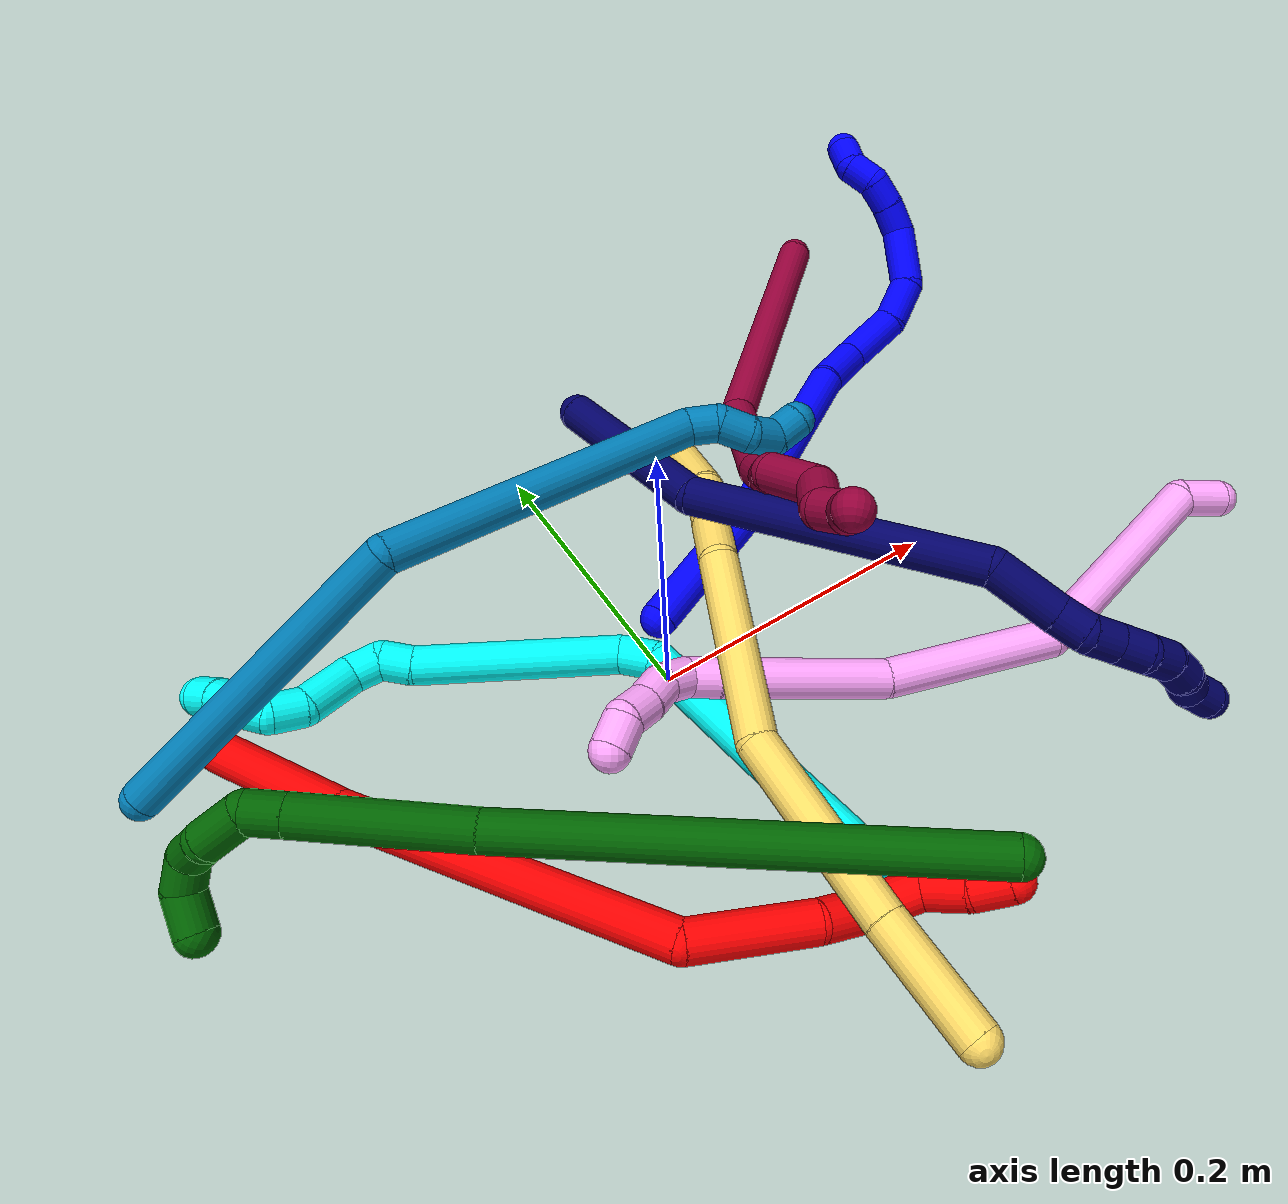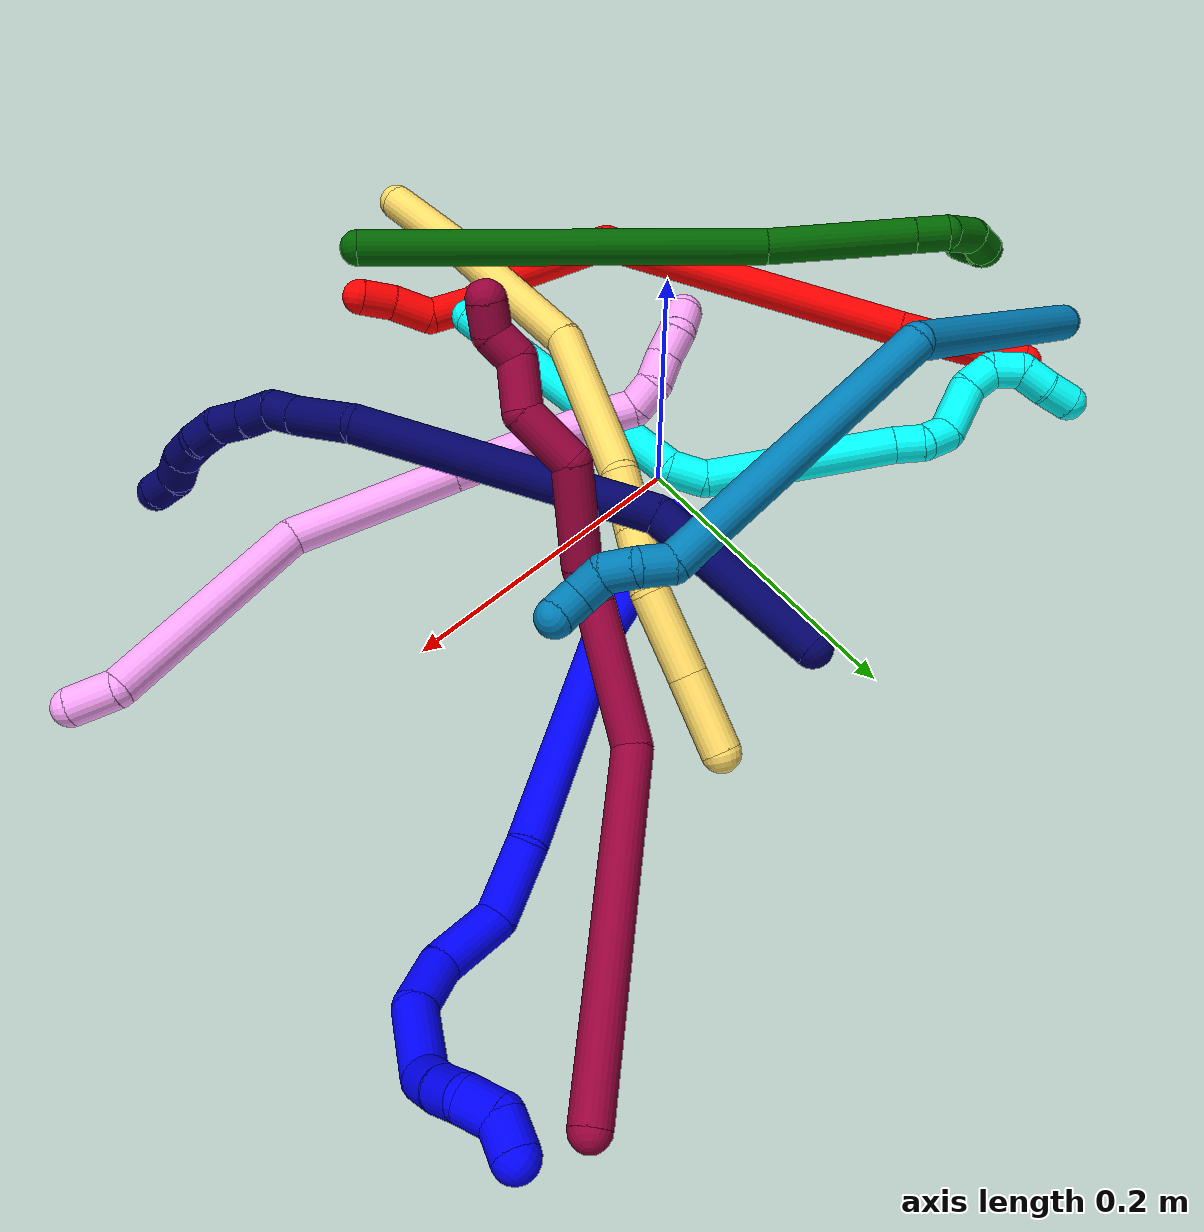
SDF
<sdf version="1.7">
 <world name="default">
  <plugin name="TubeGeneratorPlugin" filename="libtube_generator_plugin.so"/>
  <model name="photoneo_s_sensor">
   <static>1</static>
   <pose>0 0 2 1.57079 1.57079 3.14159</pose>
   <link name="link">
    <inertial><mass>0.1</mass></inertial>
    <sensor name="sensor" type="depth">
     <update_rate>30</update_rate>
     <camera>
      <horizontal_fov>1.22</horizontal_fov>
      <image><width>1920</width><height>1200</height><format>B8G8R8</format></image>
      <clip><near>0.1</near><far>4</far></clip>
      <depth_camera><output>points</output></depth_camera>
     </camera>
     <plugin name="camera_plugin" filename="libgazebo_ros_depth_camera.so">
      <baseline>0.2</baseline>
      <alwaysOn>1</alwaysOn>
      <updateRate>0.0</updateRate>
      <cameraName>camera_ir</cameraName>
      <imageTopicName>/camera/color/image_raw</imageTopicName>
      <cameraInfoTopicName>/camera/color/camera_info</cameraInfoTopicName>
      <depthImageTopicName>/camera/depth/image_raw</depthImageTopicName>
      <depthImageCameraInfoTopicName>/camera/depth/camera_info</depthImageCameraInfoTopicName>
      <pointCloudTopicName>/camera/depth/points</pointCloudTopicName>
      <frameName>fr_optical</frameName>
      <pointCloudCutoff>0.1</pointCloudCutoff>
      <pointCloudCutoffMax>2.0</pointCloudCutoffMax>
      <distortionK1>0</distortionK1>
      <distortionK2>0</distortionK2>
      <distortionK3>0</distortionK3>
      <distortionT1>0</distortionT1>
      <distortionT2>0</distortionT2>
      <CxPrime>0</CxPrime>
      <Cx>0</Cx>
      <Cy>0</Cy>
      <focalLength>0</focalLength>
      <hackBaseline>0</hackBaseline>
     </plugin>
    </sensor>
   </link>
  </model>
  <gravity>0 0 -9.8</gravity>
  <magnetic_field>6e-06 2.3e-05 -4.2e-05</magnetic_field>
  <atmosphere type="adiabatic"/>
  <physics name="default_physics" default="0" type="ode">
   <max_step_size>0.003</max_step_size>
   <real_time_factor>1</real_time_factor>
   <real_time_update_rate>1000</real_time_update_rate>
   <max_contacts>10000</max_contacts>
   <ode>
    <solver>
     <type>quick</type>
     <iters>100</iters>
     <sor>1.3</sor>
     <use_dynamic_moi_rescaling>0</use_dynamic_moi_rescaling>
    </solver>
    <constraints>
     <contact_max_correcting_vel>0</contact_max_correcting_vel>
     <contact_surface_layer>0.001</contact_surface_layer>
     <cfm>0</cfm>
     <erp>0.2</erp>
    </constraints>
   </ode>
  </physics>
  <scene><ambient>0.4 0.4 0.4 1</ambient><background>0.7 0.7 0.7 1</background><shadows>0</shadows></scene>
  <audio><device>default</device></audio>
  <spherical_coordinates>
   <surface_model>EARTH_WGS84</surface_model>
   <latitude_deg>0</latitude_deg>
   <longitude_deg>0</longitude_deg>
   <elevation>0</elevation>
   <heading_deg>0</heading_deg>
  </spherical_coordinates>
  <model name="bin">
   <static>1</static>
   <link name="bottom">
    <collision name="collision-bottom">
     <pose>0 0 -0.01 0 -0 0</pose>
     <geometry><box><size>0.8 0.6 0.02</size></box></geometry>
     <surface>
      <friction><ode><mu>100</mu><mu2>100</mu2></ode></friction>
      <contact><collide_bitmask>65535</collide_bitmask></contact>
     </surface>
    </collision>
   </link>
   <link name="west_wall">
    <collision name="collision-west_wall">
     <pose>-0.41 0 0.1 0 -0 0</pose>
     <geometry><box><size>0.02 0.6 0.2</size></box></geometry>
     <surface>
      <friction><ode><mu>100</mu><mu2>100</mu2></ode></friction>
      <contact><collide_bitmask>65535</collide_bitmask></contact>
     </surface>
    </collision>
   </link>
   <link name="east_wall">
    <collision name="collision-east_wall">
     <pose>0.41 0 0.1 0 -0 0</pose>
     <geometry><box><size>0.02 0.6 0.2</size></box></geometry>
     <surface>
      <friction><ode><mu>100</mu><mu2>100</mu2></ode></friction>
      <contact><collide_bitmask>65535</collide_bitmask></contact>
     </surface>
    </collision>
   </link>
   <link name="south_wall">
    <collision name="collision-south_wall">
     <pose>0 -0.31 0.1 0 -0 0</pose>
     <geometry><box><size>0.8 0.02 0.2</size></box></geometry>
     <surface>
      <friction><ode><mu>100</mu><mu2>100</mu2></ode></friction>
      <contact><collide_bitmask>65535</collide_bitmask></contact>
     </surface>
    </collision>
   </link>
   <link name="north_wall">
    <collision name="collision-north_wall">
     <pose>0 0.31 0.1 0 -0 0</pose>
     <geometry><box><size>0.8 0.02 0.2</size></box></geometry>
     <surface>
      <friction><ode><mu>100</mu><mu2>100</mu2></ode></friction>
      <contact><collide_bitmask>65535</collide_bitmask></contact>
     </surface>
    </collision>
   </link>
  </model>
  <model name="1">
   <static>0</static>
   <link name="1">
    <collision name="collision-cylinder-e_1_1_4">
     <pose>0.002131 -0.000476 0.049637 0.009592 0.042894 0.000206</pose>
     <geometry><cylinder><radius>0.0125</radius><length>0.09937</length></cylinder></geometry>
     <surface>
      <friction><ode><mu>1.16</mu><mu2>1.16</mu2><slip1>0</slip1><slip2>0</slip2></ode></friction>
      <contact><ode><kp>1e+06</kp><kd>1</kd><max_vel>0</max_vel><min_depth>0.001</min_depth></ode></contact>
     </surface>
    </collision>
    <visual name="visual-cylinder-e_1_1_4">
     <pose>0.002131 -0.000476 0.049637 0.009592 0.042894 0.000206</pose>
     <geometry><cylinder><radius>0.0125</radius><length>0.09937</length></cylinder></geometry>
     <material><ambient>0 0 1 1</ambient></material>
    </visual>
    <collision name="collision-cylinder-e_2_4_5">
     <pose>0.021795 0.003263 0.17088 -0.058793 0.239738 -0.007083</pose>
     <geometry><cylinder><radius>0.0125</radius><length>0.147684</length></cylinder></geometry>
     <surface>
      <friction><ode><mu>1.16</mu><mu2>1.16</mu2><slip1>0</slip1><slip2>0</slip2></ode></friction>
      <contact><ode><kp>1e+06</kp><kd>1</kd><max_vel>0</max_vel><min_depth>0.001</min_depth></ode></contact>
     </surface>
    </collision>
    <visual name="visual-cylinder-e_2_4_5">
     <pose>0.021795 0.003263 0.17088 -0.058793 0.239738 -0.007083</pose>
     <geometry><cylinder><radius>0.0125</radius><length>0.147684</length></cylinder></geometry>
     <material><ambient>0 0 1 1</ambient></material>
    </visual>
    <collision name="collision-cylinder-e_3_5_6">
     <pose>0.047104 0.003942 0.263298 0.16824 0.352907 0.030067</pose>
     <geometry><cylinder><radius>0.0125</radius><length>0.044993</length></cylinder></geometry>
     <surface>
      <friction><ode><mu>1.16</mu><mu2>1.16</mu2><slip1>0</slip1><slip2>0</slip2></ode></friction>
      <contact><ode><kp>1e+06</kp><kd>1</kd><max_vel>0</max_vel><min_depth>0.001</min_depth></ode></contact>
     </surface>
    </collision>
    <visual name="visual-cylinder-e_3_5_6">
     <pose>0.047104 0.003942 0.263298 0.16824 0.352907 0.030067</pose>
     <geometry><cylinder><radius>0.0125</radius><length>0.044993</length></cylinder></geometry>
     <material><ambient>0 0 1 1</ambient></material>
    </visual>
    <collision name="collision-cylinder-e_4_6_7">
     <pose>0.04862 -0.000766 0.305008 0.056111 -0.290582 -0.008212</pose>
     <geometry><cylinder><radius>0.0125</radius><length>0.043693</length></cylinder></geometry>
     <surface>
      <friction><ode><mu>1.16</mu><mu2>1.16</mu2><slip1>0</slip1><slip2>0</slip2></ode></friction>
      <contact><ode><kp>1e+06</kp><kd>1</kd><max_vel>0</max_vel><min_depth>0.001</min_depth></ode></contact>
     </surface>
    </collision>
    <visual name="visual-cylinder-e_4_6_7">
     <pose>0.04862 -0.000766 0.305008 0.056111 -0.290582 -0.008212</pose>
     <geometry><cylinder><radius>0.0125</radius><length>0.043693</length></cylinder></geometry>
     <material><ambient>0 0 1 1</ambient></material>
    </visual>
    <collision name="collision-cylinder-e_5_7_8">
     <pose>0.039744 0.003166 0.341162 -0.32296 -0.161238 0.026321</pose>
     <geometry><cylinder><radius>0.0125</radius><length>0.032598</length></cylinder></geometry>
     <surface>
      <friction><ode><mu>1.16</mu><mu2>1.16</mu2><slip1>0</slip1><slip2>0</slip2></ode></friction>
      <contact><ode><kp>1e+06</kp><kd>1</kd><max_vel>0</max_vel><min_depth>0.001</min_depth></ode></contact>
     </surface>
    </collision>
    <visual name="visual-cylinder-e_5_7_8">
     <pose>0.039744 0.003166 0.341162 -0.32296 -0.161238 0.026321</pose>
     <geometry><cylinder><radius>0.0125</radius><length>0.032598</length></cylinder></geometry>
     <material><ambient>0 0 1 1</ambient></material>
    </visual>
    <collision name="collision-cylinder-e_6_8_9">
     <pose>0.04069 0.024043 0.372691 -0.769736 0.155943 -0.063275</pose>
     <geometry><cylinder><radius>0.0125</radius><length>0.045879</length></cylinder></geometry>
     <surface>
      <friction><ode><mu>1.16</mu><mu2>1.16</mu2><slip1>0</slip1><slip2>0</slip2></ode></friction>
      <contact><ode><kp>1e+06</kp><kd>1</kd><max_vel>0</max_vel><min_depth>0.001</min_depth></ode></contact>
     </surface>
    </collision>
    <visual name="visual-cylinder-e_6_8_9">
     <pose>0.04069 0.024043 0.372691 -0.769736 0.155943 -0.063275</pose>
     <geometry><cylinder><radius>0.0125</radius><length>0.045879</length></cylinder></geometry>
     <material><ambient>0 0 1 1</ambient></material>
    </visual>
    <collision name="collision-cylinder-e_7_9_10">
     <pose>0.042472 0.050603 0.39172 -1.32071 -0.158531 0.123229</pose>
     <geometry><cylinder><radius>0.0125</radius><length>0.022555</length></cylinder></geometry>
     <surface>
      <friction><ode><mu>1.16</mu><mu2>1.16</mu2><slip1>0</slip1><slip2>0</slip2></ode></friction>
      <contact><ode><kp>1e+06</kp><kd>1</kd><max_vel>0</max_vel><min_depth>0.001</min_depth></ode></contact>
     </surface>
    </collision>
    <visual name="visual-cylinder-e_7_9_10">
     <pose>0.042472 0.050603 0.39172 -1.32071 -0.158531 0.123229</pose>
     <geometry><cylinder><radius>0.0125</radius><length>0.022555</length></cylinder></geometry>
     <material><ambient>0 0 1 1</ambient></material>
    </visual>
    <collision name="collision-cylinder-e_8_10_11">
     <pose>0.039908 0.07207 0.39578 -1.44919 -0.072723 0.064383</pose>
     <geometry><cylinder><radius>0.0125</radius><length>0.02157</length></cylinder></geometry>
     <surface>
      <friction><ode><mu>1.16</mu><mu2>1.16</mu2><slip1>0</slip1><slip2>0</slip2></ode></friction>
      <contact><ode><kp>1e+06</kp><kd>1</kd><max_vel>0</max_vel><min_depth>0.001</min_depth></ode></contact>
     </surface>
    </collision>
    <visual name="visual-cylinder-e_8_10_11">
     <pose>0.039908 0.07207 0.39578 -1.44919 -0.072723 0.064383</pose>
     <geometry><cylinder><radius>0.0125</radius><length>0.02157</length></cylinder></geometry>
     <material><ambient>0 0 1 1</ambient></material>
    </visual>
    <collision name="collision-cylinder-e_9_11_12">
     <pose>0.043675 0.09242 0.397363 -1.54211 0.43953 -0.427478</pose>
     <geometry><cylinder><radius>0.0125</radius><length>0.021385</length></cylinder></geometry>
     <surface>
      <friction><ode><mu>1.16</mu><mu2>1.16</mu2><slip1>0</slip1><slip2>0</slip2></ode></friction>
      <contact><ode><kp>1e+06</kp><kd>1</kd><max_vel>0</max_vel><min_depth>0.001</min_depth></ode></contact>
     </surface>
    </collision>
    <visual name="visual-cylinder-e_9_11_12">
     <pose>0.043675 0.09242 0.397363 -1.54211 0.43953 -0.427478</pose>
     <geometry><cylinder><radius>0.0125</radius><length>0.021385</length></cylinder></geometry>
     <material><ambient>0 0 1 1</ambient></material>
    </visual>
    <collision name="collision-cylinder-e_10_12_2">
     <pose>0.052854 0.108551 0.403933 -0.79845 0.474334 -0.203248</pose>
     <geometry><cylinder><radius>0.0125</radius><length>0.020272</length></cylinder></geometry>
     <surface>
      <friction><ode><mu>1.16</mu><mu2>1.16</mu2><slip1>0</slip1><slip2>0</slip2></ode></friction>
      <contact><ode><kp>1e+06</kp><kd>1</kd><max_vel>0</max_vel><min_depth>0.001</min_depth></ode></contact>
     </surface>
    </collision>
    <visual name="visual-cylinder-e_10_12_2">
     <pose>0.052854 0.108551 0.403933 -0.79845 0.474334 -0.203248</pose>
     <geometry><cylinder><radius>0.0125</radius><length>0.020272</length></cylinder></geometry>
     <material><ambient>0 0 1 1</ambient></material>
    </visual>
    <collision name="collision-sphere-2">
     <pose>0.057484 0.115009 0.410225 0 -0 0</pose>
     <geometry><sphere><radius>0.0125</radius></sphere></geometry>
     <surface>
      <friction><ode><mu>1.16</mu><mu2>1.16</mu2><slip1>0</slip1><slip2>0</slip2></ode></friction>
      <contact><ode><kp>1e+06</kp><kd>1</kd><max_vel>0</max_vel><min_depth>0.001</min_depth></ode></contact>
     </surface>
    </collision>
    <visual name="visual-sphere-2">
     <pose>0.057484 0.115009 0.410225 0 -0 0</pose>
     <geometry><sphere><radius>0.0125</radius></sphere></geometry>
     <material><ambient>0 0 1 1</ambient></material>
    </visual>
    <collision name="collision-sphere-12">
     <pose>0.048225 0.102092 0.39764 0 -0 0</pose>
     <geometry><sphere><radius>0.0125</radius></sphere></geometry>
     <surface>
      <friction><ode><mu>1.16</mu><mu2>1.16</mu2><slip1>0</slip1><slip2>0</slip2></ode></friction>
      <contact><ode><kp>1e+06</kp><kd>1</kd><max_vel>0</max_vel><min_depth>0.001</min_depth></ode></contact>
     </surface>
    </collision>
    <visual name="visual-sphere-12">
     <pose>0.048225 0.102092 0.39764 0 -0 0</pose>
     <geometry><sphere><radius>0.0125</radius></sphere></geometry>
     <material><ambient>0 0 1 1</ambient></material>
    </visual>
    <collision name="collision-sphere-11">
     <pose>0.039125 0.082747 0.397085 0 -0 0</pose>
     <geometry><sphere><radius>0.0125</radius></sphere></geometry>
     <surface>
      <friction><ode><mu>1.16</mu><mu2>1.16</mu2><slip1>0</slip1><slip2>0</slip2></ode></friction>
      <contact><ode><kp>1e+06</kp><kd>1</kd><max_vel>0</max_vel><min_depth>0.001</min_depth></ode></contact>
     </surface>
    </collision>
    <visual name="visual-sphere-11">
     <pose>0.039125 0.082747 0.397085 0 -0 0</pose>
     <geometry><sphere><radius>0.0125</radius></sphere></geometry>
     <material><ambient>0 0 1 1</ambient></material>
    </visual>
    <collision name="collision-sphere-10">
     <pose>0.040692 0.061393 0.394476 0 -0 0</pose>
     <geometry><sphere><radius>0.0125</radius></sphere></geometry>
     <surface>
      <friction><ode><mu>1.16</mu><mu2>1.16</mu2><slip1>0</slip1><slip2>0</slip2></ode></friction>
      <contact><ode><kp>1e+06</kp><kd>1</kd><max_vel>0</max_vel><min_depth>0.001</min_depth></ode></contact>
     </surface>
    </collision>
    <visual name="visual-sphere-10">
     <pose>0.040692 0.061393 0.394476 0 -0 0</pose>
     <geometry><sphere><radius>0.0125</radius></sphere></geometry>
     <material><ambient>0 0 1 1</ambient></material>
    </visual>
    <collision name="collision-sphere-9">
     <pose>0.044253 0.039814 0.388964 0 -0 0</pose>
     <geometry><sphere><radius>0.0125</radius></sphere></geometry>
     <surface>
      <friction><ode><mu>1.16</mu><mu2>1.16</mu2><slip1>0</slip1><slip2>0</slip2></ode></friction>
      <contact><ode><kp>1e+06</kp><kd>1</kd><max_vel>0</max_vel><min_depth>0.001</min_depth></ode></contact>
     </surface>
    </collision>
    <visual name="visual-sphere-9">
     <pose>0.044253 0.039814 0.388964 0 -0 0</pose>
     <geometry><sphere><radius>0.0125</radius></sphere></geometry>
     <material><ambient>0 0 1 1</ambient></material>
    </visual>
    <collision name="collision-sphere-4">
     <pose>0.004261 -0.000952 0.099274 0 -0 0</pose>
     <geometry><sphere><radius>0.0125</radius></sphere></geometry>
     <surface>
      <friction><ode><mu>1.16</mu><mu2>1.16</mu2><slip1>0</slip1><slip2>0</slip2></ode></friction>
      <contact><ode><kp>1e+06</kp><kd>1</kd><max_vel>0</max_vel><min_depth>0.001</min_depth></ode></contact>
     </surface>
    </collision>
    <visual name="visual-sphere-4">
     <pose>0.004261 -0.000952 0.099274 0 -0 0</pose>
     <geometry><sphere><radius>0.0125</radius></sphere></geometry>
     <material><ambient>0 0 1 1</ambient></material>
    </visual>
    <collision name="collision-sphere-1">
     <geometry><sphere><radius>0.0125</radius></sphere></geometry>
     <surface>
      <friction><ode><mu>1.16</mu><mu2>1.16</mu2><slip1>0</slip1><slip2>0</slip2></ode></friction>
      <contact><ode><kp>1e+06</kp><kd>1</kd><max_vel>0</max_vel><min_depth>0.001</min_depth></ode></contact>
     </surface>
    </collision>
    <visual name="visual-sphere-1">
     <geometry><sphere><radius>0.0125</radius></sphere></geometry>
     <material><ambient>0 0 1 1</ambient></material>
    </visual>
    <collision name="collision-sphere-8">
     <pose>0.037127 0.008272 0.356418 0 -0 0</pose>
     <geometry><sphere><radius>0.0125</radius></sphere></geometry>
     <surface>
      <friction><ode><mu>1.16</mu><mu2>1.16</mu2><slip1>0</slip1><slip2>0</slip2></ode></friction>
      <contact><ode><kp>1e+06</kp><kd>1</kd><max_vel>0</max_vel><min_depth>0.001</min_depth></ode></contact>
     </surface>
    </collision>
    <visual name="visual-sphere-8">
     <pose>0.037127 0.008272 0.356418 0 -0 0</pose>
     <geometry><sphere><radius>0.0125</radius></sphere></geometry>
     <material><ambient>0 0 1 1</ambient></material>
    </visual>
    <collision name="collision-sphere-5">
     <pose>0.039328 0.007477 0.242486 0 -0 0</pose>
     <geometry><sphere><radius>0.0125</radius></sphere></geometry>
     <surface>
      <friction><ode><mu>1.16</mu><mu2>1.16</mu2><slip1>0</slip1><slip2>0</slip2></ode></friction>
      <contact><ode><kp>1e+06</kp><kd>1</kd><max_vel>0</max_vel><min_depth>0.001</min_depth></ode></contact>
     </surface>
    </collision>
    <visual name="visual-sphere-5">
     <pose>0.039328 0.007477 0.242486 0 -0 0</pose>
     <geometry><sphere><radius>0.0125</radius></sphere></geometry>
     <material><ambient>0 0 1 1</ambient></material>
    </visual>
    <collision name="collision-sphere-6">
     <pose>0.054879 0.000408 0.28411 0 -0 0</pose>
     <geometry><sphere><radius>0.0125</radius></sphere></geometry>
     <surface>
      <friction><ode><mu>1.16</mu><mu2>1.16</mu2><slip1>0</slip1><slip2>0</slip2></ode></friction>
      <contact><ode><kp>1e+06</kp><kd>1</kd><max_vel>0</max_vel><min_depth>0.001</min_depth></ode></contact>
     </surface>
    </collision>
    <visual name="visual-sphere-6">
     <pose>0.054879 0.000408 0.28411 0 -0 0</pose>
     <geometry><sphere><radius>0.0125</radius></sphere></geometry>
     <material><ambient>0 0 1 1</ambient></material>
    </visual>
    <collision name="collision-sphere-7">
     <pose>0.042361 -0.00194 0.325906 0 -0 0</pose>
     <geometry><sphere><radius>0.0125</radius></sphere></geometry>
     <surface>
      <friction><ode><mu>1.16</mu><mu2>1.16</mu2><slip1>0</slip1><slip2>0</slip2></ode></friction>
      <contact><ode><kp>1e+06</kp><kd>1</kd><max_vel>0</max_vel><min_depth>0.001</min_depth></ode></contact>
     </surface>
    </collision>
    <visual name="visual-sphere-7">
     <pose>0.042361 -0.00194 0.325906 0 -0 0</pose>
     <geometry><sphere><radius>0.0125</radius></sphere></geometry>
     <material><ambient>0 0 1 1</ambient></material>
    </visual>
    <inertial>
     <pose>0.029322 0.017315 0.235241 0 -0 0</pose>
     <mass>0.5</mass>
     <inertia>
      <ixx>0.000391</ixx>
      <ixy>0</ixy>
      <ixz>0</ixz>
      <iyy>0.000397</iyy>
      <iyz>0</iyz>
      <izz>-6.6e-05</izz>
     </inertia>
    </inertial>
   </link>
   <pose>0.016486 0.036402 0.011498 1.35673 0.833263 1.7539</pose>
  </model>
  <model name="2">
   <static>0</static>
   <link name="2">
    <collision name="collision-cylinder-e_1_1_4">
     <pose>0.029168 -0.032869 0.005252 1.41236 0.719556 0.620894</pose>
     <geometry><cylinder><radius>0.0125</radius><length>0.088514</length></cylinder></geometry>
     <surface>
      <friction><ode><mu>1.16</mu><mu2>1.16</mu2><slip1>0</slip1><slip2>0</slip2></ode></friction>
      <contact><ode><kp>1e+06</kp><kd>1</kd><max_vel>0</max_vel><min_depth>0.001</min_depth></ode></contact>
     </surface>
    </collision>
    <visual name="visual-cylinder-e_1_1_4">
     <pose>0.029168 -0.032869 0.005252 1.41236 0.719556 0.620894</pose>
     <geometry><cylinder><radius>0.0125</radius><length>0.088514</length></cylinder></geometry>
     <material><ambient>1 0 0 1</ambient></material>
    </visual>
    <collision name="collision-cylinder-e_2_4_5">
     <pose>0.137964 -0.14024 0.023628 1.39642 0.811017 0.691612</pose>
     <geometry><cylinder><radius>0.0125</radius><length>0.219669</length></cylinder></geometry>
     <surface>
      <friction><ode><mu>1.16</mu><mu2>1.16</mu2><slip1>0</slip1><slip2>0</slip2></ode></friction>
      <contact><ode><kp>1e+06</kp><kd>1</kd><max_vel>0</max_vel><min_depth>0.001</min_depth></ode></contact>
     </surface>
    </collision>
    <visual name="visual-cylinder-e_2_4_5">
     <pose>0.137964 -0.14024 0.023628 1.39642 0.811017 0.691612</pose>
     <geometry><cylinder><radius>0.0125</radius><length>0.219669</length></cylinder></geometry>
     <material><ambient>1 0 0 1</ambient></material>
    </visual>
    <collision name="collision-cylinder-e_3_5_6">
     <pose>0.243292 -0.23414 0.017694 2.34737 0.757141 1.51786</pose>
     <geometry><cylinder><radius>0.0125</radius><length>0.074833</length></cylinder></geometry>
     <surface>
      <friction><ode><mu>1.16</mu><mu2>1.16</mu2><slip1>0</slip1><slip2>0</slip2></ode></friction>
      <contact><ode><kp>1e+06</kp><kd>1</kd><max_vel>0</max_vel><min_depth>0.001</min_depth></ode></contact>
     </surface>
    </collision>
    <visual name="visual-cylinder-e_3_5_6">
     <pose>0.243292 -0.23414 0.017694 2.34737 0.757141 1.51786</pose>
     <geometry><cylinder><radius>0.0125</radius><length>0.074833</length></cylinder></geometry>
     <material><ambient>1 0 0 1</ambient></material>
    </visual>
    <collision name="collision-cylinder-e_4_6_7">
     <pose>0.276233 -0.261464 -0.012864 2.53814 0.478361 1.3292</pose>
     <geometry><cylinder><radius>0.0125</radius><length>0.031465</length></cylinder></geometry>
     <surface>
      <friction><ode><mu>1.16</mu><mu2>1.16</mu2><slip1>0</slip1><slip2>0</slip2></ode></friction>
      <contact><ode><kp>1e+06</kp><kd>1</kd><max_vel>0</max_vel><min_depth>0.001</min_depth></ode></contact>
     </surface>
    </collision>
    <visual name="visual-cylinder-e_4_6_7">
     <pose>0.276233 -0.261464 -0.012864 2.53814 0.478361 1.3292</pose>
     <geometry><cylinder><radius>0.0125</radius><length>0.031465</length></cylinder></geometry>
     <material><ambient>1 0 0 1</ambient></material>
    </visual>
    <collision name="collision-cylinder-e_5_7_8">
     <pose>0.297199 -0.274221 -0.032709 2.61683 0.958367 2.18742</pose>
     <geometry><cylinder><radius>0.0125</radius><length>0.033546</length></cylinder></geometry>
     <surface>
      <friction><ode><mu>1.16</mu><mu2>1.16</mu2><slip1>0</slip1><slip2>0</slip2></ode></friction>
      <contact><ode><kp>1e+06</kp><kd>1</kd><max_vel>0</max_vel><min_depth>0.001</min_depth></ode></contact>
     </surface>
    </collision>
    <visual name="visual-cylinder-e_5_7_8">
     <pose>0.297199 -0.274221 -0.032709 2.61683 0.958367 2.18742</pose>
     <geometry><cylinder><radius>0.0125</radius><length>0.033546</length></cylinder></geometry>
     <material><ambient>1 0 0 1</ambient></material>
    </visual>
    <collision name="collision-cylinder-e_6_8_9">
     <pose>0.323832 -0.284407 -0.039395 1.27049 1.16104 0.900756</pose>
     <geometry><cylinder><radius>0.0125</radius><length>0.028146</length></cylinder></geometry>
     <surface>
      <friction><ode><mu>1.16</mu><mu2>1.16</mu2><slip1>0</slip1><slip2>0</slip2></ode></friction>
      <contact><ode><kp>1e+06</kp><kd>1</kd><max_vel>0</max_vel><min_depth>0.001</min_depth></ode></contact>
     </surface>
    </collision>
    <visual name="visual-cylinder-e_6_8_9">
     <pose>0.323832 -0.284407 -0.039395 1.27049 1.16104 0.900756</pose>
     <geometry><cylinder><radius>0.0125</radius><length>0.028146</length></cylinder></geometry>
     <material><ambient>1 0 0 1</ambient></material>
    </visual>
    <collision name="collision-cylinder-e_7_9_2">
     <pose>0.348218 -0.292795 -0.038732 1.88796 1.29955 1.61876</pose>
     <geometry><cylinder><radius>0.0125</radius><length>0.023828</length></cylinder></geometry>
     <surface>
      <friction><ode><mu>1.16</mu><mu2>1.16</mu2><slip1>0</slip1><slip2>0</slip2></ode></friction>
      <contact><ode><kp>1e+06</kp><kd>1</kd><max_vel>0</max_vel><min_depth>0.001</min_depth></ode></contact>
     </surface>
    </collision>
    <visual name="visual-cylinder-e_7_9_2">
     <pose>0.348218 -0.292795 -0.038732 1.88796 1.29955 1.61876</pose>
     <geometry><cylinder><radius>0.0125</radius><length>0.023828</length></cylinder></geometry>
     <material><ambient>1 0 0 1</ambient></material>
    </visual>
    <collision name="collision-sphere-2">
     <pose>0.359697 -0.295828 -0.039728 0 -0 0</pose>
     <geometry><sphere><radius>0.0125</radius></sphere></geometry>
     <surface>
      <friction><ode><mu>1.16</mu><mu2>1.16</mu2><slip1>0</slip1><slip2>0</slip2></ode></friction>
      <contact><ode><kp>1e+06</kp><kd>1</kd><max_vel>0</max_vel><min_depth>0.001</min_depth></ode></contact>
     </surface>
    </collision>
    <visual name="visual-sphere-2">
     <pose>0.359697 -0.295828 -0.039728 0 -0 0</pose>
     <geometry><sphere><radius>0.0125</radius></sphere></geometry>
     <material><ambient>1 0 0 1</ambient></material>
    </visual>
    <collision name="collision-sphere-9">
     <pose>0.33674 -0.289763 -0.037736 0 -0 0</pose>
     <geometry><sphere><radius>0.0125</radius></sphere></geometry>
     <surface>
      <friction><ode><mu>1.16</mu><mu2>1.16</mu2><slip1>0</slip1><slip2>0</slip2></ode></friction>
      <contact><ode><kp>1e+06</kp><kd>1</kd><max_vel>0</max_vel><min_depth>0.001</min_depth></ode></contact>
     </surface>
    </collision>
    <visual name="visual-sphere-9">
     <pose>0.33674 -0.289763 -0.037736 0 -0 0</pose>
     <geometry><sphere><radius>0.0125</radius></sphere></geometry>
     <material><ambient>1 0 0 1</ambient></material>
    </visual>
    <collision name="collision-sphere-4">
     <pose>0.058335 -0.065737 0.010503 0 -0 0</pose>
     <geometry><sphere><radius>0.0125</radius></sphere></geometry>
     <surface>
      <friction><ode><mu>1.16</mu><mu2>1.16</mu2><slip1>0</slip1><slip2>0</slip2></ode></friction>
      <contact><ode><kp>1e+06</kp><kd>1</kd><max_vel>0</max_vel><min_depth>0.001</min_depth></ode></contact>
     </surface>
    </collision>
    <visual name="visual-sphere-4">
     <pose>0.058335 -0.065737 0.010503 0 -0 0</pose>
     <geometry><sphere><radius>0.0125</radius></sphere></geometry>
     <material><ambient>1 0 0 1</ambient></material>
    </visual>
    <collision name="collision-sphere-1">
     <geometry><sphere><radius>0.0125</radius></sphere></geometry>
     <surface>
      <friction><ode><mu>1.16</mu><mu2>1.16</mu2><slip1>0</slip1><slip2>0</slip2></ode></friction>
      <contact><ode><kp>1e+06</kp><kd>1</kd><max_vel>0</max_vel><min_depth>0.001</min_depth></ode></contact>
     </surface>
    </collision>
    <visual name="visual-sphere-1">
     <geometry><sphere><radius>0.0125</radius></sphere></geometry>
     <material><ambient>1 0 0 1</ambient></material>
    </visual>
    <collision name="collision-sphere-8">
     <pose>0.310924 -0.279051 -0.041053 0 -0 0</pose>
     <geometry><sphere><radius>0.0125</radius></sphere></geometry>
     <surface>
      <friction><ode><mu>1.16</mu><mu2>1.16</mu2><slip1>0</slip1><slip2>0</slip2></ode></friction>
      <contact><ode><kp>1e+06</kp><kd>1</kd><max_vel>0</max_vel><min_depth>0.001</min_depth></ode></contact>
     </surface>
    </collision>
    <visual name="visual-sphere-8">
     <pose>0.310924 -0.279051 -0.041053 0 -0 0</pose>
     <geometry><sphere><radius>0.0125</radius></sphere></geometry>
     <material><ambient>1 0 0 1</ambient></material>
    </visual>
    <collision name="collision-sphere-5">
     <pose>0.217592 -0.214742 0.036753 0 -0 0</pose>
     <geometry><sphere><radius>0.0125</radius></sphere></geometry>
     <surface>
      <friction><ode><mu>1.16</mu><mu2>1.16</mu2><slip1>0</slip1><slip2>0</slip2></ode></friction>
      <contact><ode><kp>1e+06</kp><kd>1</kd><max_vel>0</max_vel><min_depth>0.001</min_depth></ode></contact>
     </surface>
    </collision>
    <visual name="visual-sphere-5">
     <pose>0.217592 -0.214742 0.036753 0 -0 0</pose>
     <geometry><sphere><radius>0.0125</radius></sphere></geometry>
     <material><ambient>1 0 0 1</ambient></material>
    </visual>
    <collision name="collision-sphere-6">
     <pose>0.268991 -0.253538 -0.001364 0 -0 0</pose>
     <geometry><sphere><radius>0.0125</radius></sphere></geometry>
     <surface>
      <friction><ode><mu>1.16</mu><mu2>1.16</mu2><slip1>0</slip1><slip2>0</slip2></ode></friction>
      <contact><ode><kp>1e+06</kp><kd>1</kd><max_vel>0</max_vel><min_depth>0.001</min_depth></ode></contact>
     </surface>
    </collision>
    <visual name="visual-sphere-6">
     <pose>0.268991 -0.253538 -0.001364 0 -0 0</pose>
     <geometry><sphere><radius>0.0125</radius></sphere></geometry>
     <material><ambient>1 0 0 1</ambient></material>
    </visual>
    <collision name="collision-sphere-7">
     <pose>0.283475 -0.26939 -0.024364 0 -0 0</pose>
     <geometry><sphere><radius>0.0125</radius></sphere></geometry>
     <surface>
      <friction><ode><mu>1.16</mu><mu2>1.16</mu2><slip1>0</slip1><slip2>0</slip2></ode></friction>
      <contact><ode><kp>1e+06</kp><kd>1</kd><max_vel>0</max_vel><min_depth>0.001</min_depth></ode></contact>
     </surface>
    </collision>
    <visual name="visual-sphere-7">
     <pose>0.283475 -0.26939 -0.024364 0 -0 0</pose>
     <geometry><sphere><radius>0.0125</radius></sphere></geometry>
     <material><ambient>1 0 0 1</ambient></material>
    </visual>
    <inertial>
     <pose>0.174335 -0.167289 0.006891 0 -0 0</pose>
     <mass>0.5</mass>
     <inertia>
      <ixx>0.000993</ixx>
      <ixy>0</ixy>
      <ixz>0</ixz>
      <iyy>0.001012</iyy>
      <iyz>0</iyz>
      <izz>-5.1e-05</izz>
     </inertia>
    </inertial>
   </link>
   <pose>-0.253836 0.100349 0.011498 0.919549 -0.679528 -0.478778</pose>
  </model>
  <model name="3">
   <static>0</static>
   <link name="3">
    <collision name="collision-cylinder-e_1_1_4">
     <pose>-0.062923 0.046232 0.050217 -0.744097 -0.744751 0.302512</pose>
     <geometry><cylinder><radius>0.0125</radius><length>0.185671</length></cylinder></geometry>
     <surface>
      <friction><ode><mu>1.16</mu><mu2>1.16</mu2><slip1>0</slip1><slip2>0</slip2></ode></friction>
      <contact><ode><kp>1e+06</kp><kd>1</kd><max_vel>0</max_vel><min_depth>0.001</min_depth></ode></contact>
     </surface>
    </collision>
    <visual name="visual-cylinder-e_1_1_4">
     <pose>-0.062923 0.046232 0.050217 -0.744097 -0.744751 0.302512</pose>
     <geometry><cylinder><radius>0.0125</radius><length>0.185671</length></cylinder></geometry>
     <material><ambient>0.003922 1 0.996078 1</ambient></material>
    </visual>
    <collision name="collision-cylinder-e_2_4_5">
     <pose>-0.13251 0.093816 0.110842 -0.129252 -0.56576 0.037618</pose>
     <geometry><cylinder><radius>0.0125</radius><length>0.024865</length></cylinder></geometry>
     <surface>
      <friction><ode><mu>1.16</mu><mu2>1.16</mu2><slip1>0</slip1><slip2>0</slip2></ode></friction>
      <contact><ode><kp>1e+06</kp><kd>1</kd><max_vel>0</max_vel><min_depth>0.001</min_depth></ode></contact>
     </surface>
    </collision>
    <visual name="visual-cylinder-e_2_4_5">
     <pose>-0.13251 0.093816 0.110842 -0.129252 -0.56576 0.037618</pose>
     <geometry><cylinder><radius>0.0125</radius><length>0.024865</length></cylinder></geometry>
     <material><ambient>0.003922 1 0.996078 1</ambient></material>
    </visual>
    <collision name="collision-cylinder-e_3_5_6">
     <pose>-0.146506 0.093132 0.185987 0.031457 -0.112718 -0.001775</pose>
     <geometry><cylinder><radius>0.0125</radius><length>0.130364</length></cylinder></geometry>
     <surface>
      <friction><ode><mu>1.16</mu><mu2>1.16</mu2><slip1>0</slip1><slip2>0</slip2></ode></friction>
      <contact><ode><kp>1e+06</kp><kd>1</kd><max_vel>0</max_vel><min_depth>0.001</min_depth></ode></contact>
     </surface>
    </collision>
    <visual name="visual-cylinder-e_3_5_6">
     <pose>-0.146506 0.093132 0.185987 0.031457 -0.112718 -0.001775</pose>
     <geometry><cylinder><radius>0.0125</radius><length>0.130364</length></cylinder></geometry>
     <material><ambient>0.003922 1 0.996078 1</ambient></material>
    </visual>
    <collision name="collision-cylinder-e_4_6_7">
     <pose>-0.155581 0.093027 0.260589 -0.193382 -0.171708 0.016695</pose>
     <geometry><cylinder><radius>0.0125</radius><length>0.020407</length></cylinder></geometry>
     <surface>
      <friction><ode><mu>1.16</mu><mu2>1.16</mu2><slip1>0</slip1><slip2>0</slip2></ode></friction>
      <contact><ode><kp>1e+06</kp><kd>1</kd><max_vel>0</max_vel><min_depth>0.001</min_depth></ode></contact>
     </surface>
    </collision>
    <visual name="visual-cylinder-e_4_6_7">
     <pose>-0.155581 0.093027 0.260589 -0.193382 -0.171708 0.016695</pose>
     <geometry><cylinder><radius>0.0125</radius><length>0.020407</length></cylinder></geometry>
     <material><ambient>0.003922 1 0.996078 1</ambient></material>
    </visual>
    <collision name="collision-cylinder-e_5_7_8">
     <pose>-0.15732 0.090866 0.279729 0.415621 0.00046 9.7e-05</pose>
     <geometry><cylinder><radius>0.0125</radius><length>0.020274</length></cylinder></geometry>
     <surface>
      <friction><ode><mu>1.16</mu><mu2>1.16</mu2><slip1>0</slip1><slip2>0</slip2></ode></friction>
      <contact><ode><kp>1e+06</kp><kd>1</kd><max_vel>0</max_vel><min_depth>0.001</min_depth></ode></contact>
     </surface>
    </collision>
    <visual name="visual-cylinder-e_5_7_8">
     <pose>-0.15732 0.090866 0.279729 0.415621 0.00046 9.7e-05</pose>
     <geometry><cylinder><radius>0.0125</radius><length>0.020274</length></cylinder></geometry>
     <material><ambient>0.003922 1 0.996078 1</ambient></material>
    </visual>
    <collision name="collision-cylinder-e_6_8_9">
     <pose>-0.145518 0.079703 0.30179 0.505072 0.67924 0.181837</pose>
     <geometry><cylinder><radius>0.0125</radius><length>0.03756</length></cylinder></geometry>
     <surface>
      <friction><ode><mu>1.16</mu><mu2>1.16</mu2><slip1>0</slip1><slip2>0</slip2></ode></friction>
      <contact><ode><kp>1e+06</kp><kd>1</kd><max_vel>0</max_vel><min_depth>0.001</min_depth></ode></contact>
     </surface>
    </collision>
    <visual name="visual-cylinder-e_6_8_9">
     <pose>-0.145518 0.079703 0.30179 0.505072 0.67924 0.181837</pose>
     <geometry><cylinder><radius>0.0125</radius><length>0.03756</length></cylinder></geometry>
     <material><ambient>0.003922 1 0.996078 1</ambient></material>
    </visual>
    <collision name="collision-cylinder-e_7_9_10">
     <pose>-0.130281 0.071685 0.324245 0.097701 0.340294 0.016799</pose>
     <geometry><cylinder><radius>0.0125</radius><length>0.02061</length></cylinder></geometry>
     <surface>
      <friction><ode><mu>1.16</mu><mu2>1.16</mu2><slip1>0</slip1><slip2>0</slip2></ode></friction>
      <contact><ode><kp>1e+06</kp><kd>1</kd><max_vel>0</max_vel><min_depth>0.001</min_depth></ode></contact>
     </surface>
    </collision>
    <visual name="visual-cylinder-e_7_9_10">
     <pose>-0.130281 0.071685 0.324245 0.097701 0.340294 0.016799</pose>
     <geometry><cylinder><radius>0.0125</radius><length>0.02061</length></cylinder></geometry>
     <material><ambient>0.003922 1 0.996078 1</ambient></material>
    </visual>
    <collision name="collision-cylinder-e_8_10_11">
     <pose>-0.129648 0.072994 0.343244 -0.23721 -0.284371 0.034114</pose>
     <geometry><cylinder><radius>0.0125</radius><length>0.020005</length></cylinder></geometry>
     <surface>
      <friction><ode><mu>1.16</mu><mu2>1.16</mu2><slip1>0</slip1><slip2>0</slip2></ode></friction>
      <contact><ode><kp>1e+06</kp><kd>1</kd><max_vel>0</max_vel><min_depth>0.001</min_depth></ode></contact>
     </surface>
    </collision>
    <visual name="visual-cylinder-e_8_10_11">
     <pose>-0.129648 0.072994 0.343244 -0.23721 -0.284371 0.034114</pose>
     <geometry><cylinder><radius>0.0125</radius><length>0.020005</length></cylinder></geometry>
     <material><ambient>0.003922 1 0.996078 1</ambient></material>
    </visual>
    <collision name="collision-cylinder-e_9_11_12">
     <pose>-0.140208 0.076297 0.358947 -0.162996 -0.876447 0.076514</pose>
     <geometry><cylinder><radius>0.0125</radius><length>0.020179</length></cylinder></geometry>
     <surface>
      <friction><ode><mu>1.16</mu><mu2>1.16</mu2><slip1>0</slip1><slip2>0</slip2></ode></friction>
      <contact><ode><kp>1e+06</kp><kd>1</kd><max_vel>0</max_vel><min_depth>0.001</min_depth></ode></contact>
     </surface>
    </collision>
    <visual name="visual-cylinder-e_9_11_12">
     <pose>-0.140208 0.076297 0.358947 -0.162996 -0.876447 0.076514</pose>
     <geometry><cylinder><radius>0.0125</radius><length>0.020179</length></cylinder></geometry>
     <material><ambient>0.003922 1 0.996078 1</ambient></material>
    </visual>
    <collision name="collision-cylinder-e_10_12_2">
     <pose>-0.155146 0.076704 0.372291 0.09166 -0.798203 -0.038678</pose>
     <geometry><cylinder><radius>0.0125</radius><length>0.020066</length></cylinder></geometry>
     <surface>
      <friction><ode><mu>1.16</mu><mu2>1.16</mu2><slip1>0</slip1><slip2>0</slip2></ode></friction>
      <contact><ode><kp>1e+06</kp><kd>1</kd><max_vel>0</max_vel><min_depth>0.001</min_depth></ode></contact>
     </surface>
    </collision>
    <visual name="visual-cylinder-e_10_12_2">
     <pose>-0.155146 0.076704 0.372291 0.09166 -0.798203 -0.038678</pose>
     <geometry><cylinder><radius>0.0125</radius><length>0.020066</length></cylinder></geometry>
     <material><ambient>0.003922 1 0.996078 1</ambient></material>
    </visual>
    <collision name="collision-sphere-2">
     <pose>-0.162331 0.076063 0.379264 0 -0 0</pose>
     <geometry><sphere><radius>0.0125</radius></sphere></geometry>
     <surface>
      <friction><ode><mu>1.16</mu><mu2>1.16</mu2><slip1>0</slip1><slip2>0</slip2></ode></friction>
      <contact><ode><kp>1e+06</kp><kd>1</kd><max_vel>0</max_vel><min_depth>0.001</min_depth></ode></contact>
     </surface>
    </collision>
    <visual name="visual-sphere-2">
     <pose>-0.162331 0.076063 0.379264 0 -0 0</pose>
     <geometry><sphere><radius>0.0125</radius></sphere></geometry>
     <material><ambient>0.003922 1 0.996078 1</ambient></material>
    </visual>
    <collision name="collision-sphere-12">
     <pose>-0.147961 0.077345 0.365317 0 -0 0</pose>
     <geometry><sphere><radius>0.0125</radius></sphere></geometry>
     <surface>
      <friction><ode><mu>1.16</mu><mu2>1.16</mu2><slip1>0</slip1><slip2>0</slip2></ode></friction>
      <contact><ode><kp>1e+06</kp><kd>1</kd><max_vel>0</max_vel><min_depth>0.001</min_depth></ode></contact>
     </surface>
    </collision>
    <visual name="visual-sphere-12">
     <pose>-0.147961 0.077345 0.365317 0 -0 0</pose>
     <geometry><sphere><radius>0.0125</radius></sphere></geometry>
     <material><ambient>0.003922 1 0.996078 1</ambient></material>
    </visual>
    <collision name="collision-sphere-11">
     <pose>-0.132454 0.07525 0.352576 0 -0 0</pose>
     <geometry><sphere><radius>0.0125</radius></sphere></geometry>
     <surface>
      <friction><ode><mu>1.16</mu><mu2>1.16</mu2><slip1>0</slip1><slip2>0</slip2></ode></friction>
      <contact><ode><kp>1e+06</kp><kd>1</kd><max_vel>0</max_vel><min_depth>0.001</min_depth></ode></contact>
     </surface>
    </collision>
    <visual name="visual-sphere-11">
     <pose>-0.132454 0.07525 0.352576 0 -0 0</pose>
     <geometry><sphere><radius>0.0125</radius></sphere></geometry>
     <material><ambient>0.003922 1 0.996078 1</ambient></material>
    </visual>
    <collision name="collision-sphere-10">
     <pose>-0.126842 0.070738 0.333912 0 -0 0</pose>
     <geometry><sphere><radius>0.0125</radius></sphere></geometry>
     <surface>
      <friction><ode><mu>1.16</mu><mu2>1.16</mu2><slip1>0</slip1><slip2>0</slip2></ode></friction>
      <contact><ode><kp>1e+06</kp><kd>1</kd><max_vel>0</max_vel><min_depth>0.001</min_depth></ode></contact>
     </surface>
    </collision>
    <visual name="visual-sphere-10">
     <pose>-0.126842 0.070738 0.333912 0 -0 0</pose>
     <geometry><sphere><radius>0.0125</radius></sphere></geometry>
     <material><ambient>0.003922 1 0.996078 1</ambient></material>
    </visual>
    <collision name="collision-sphere-9">
     <pose>-0.13372 0.072633 0.314577 0 -0 0</pose>
     <geometry><sphere><radius>0.0125</radius></sphere></geometry>
     <surface>
      <friction><ode><mu>1.16</mu><mu2>1.16</mu2><slip1>0</slip1><slip2>0</slip2></ode></friction>
      <contact><ode><kp>1e+06</kp><kd>1</kd><max_vel>0</max_vel><min_depth>0.001</min_depth></ode></contact>
     </surface>
    </collision>
    <visual name="visual-sphere-9">
     <pose>-0.13372 0.072633 0.314577 0 -0 0</pose>
     <geometry><sphere><radius>0.0125</radius></sphere></geometry>
     <material><ambient>0.003922 1 0.996078 1</ambient></material>
    </visual>
    <collision name="collision-sphere-4">
     <pose>-0.125845 0.092463 0.100435 0 -0 0</pose>
     <geometry><sphere><radius>0.0125</radius></sphere></geometry>
     <surface>
      <friction><ode><mu>1.16</mu><mu2>1.16</mu2><slip1>0</slip1><slip2>0</slip2></ode></friction>
      <contact><ode><kp>1e+06</kp><kd>1</kd><max_vel>0</max_vel><min_depth>0.001</min_depth></ode></contact>
     </surface>
    </collision>
    <visual name="visual-sphere-4">
     <pose>-0.125845 0.092463 0.100435 0 -0 0</pose>
     <geometry><sphere><radius>0.0125</radius></sphere></geometry>
     <material><ambient>0.003922 1 0.996078 1</ambient></material>
    </visual>
    <collision name="collision-sphere-1">
     <geometry><sphere><radius>0.0125</radius></sphere></geometry>
     <surface>
      <friction><ode><mu>1.16</mu><mu2>1.16</mu2><slip1>0</slip1><slip2>0</slip2></ode></friction>
      <contact><ode><kp>1e+06</kp><kd>1</kd><max_vel>0</max_vel><min_depth>0.001</min_depth></ode></contact>
     </surface>
    </collision>
    <visual name="visual-sphere-1">
     <geometry><sphere><radius>0.0125</radius></sphere></geometry>
     <material><ambient>0.003922 1 0.996078 1</ambient></material>
    </visual>
    <collision name="collision-sphere-8">
     <pose>-0.157316 0.086773 0.289003 0 -0 0</pose>
     <geometry><sphere><radius>0.0125</radius></sphere></geometry>
     <surface>
      <friction><ode><mu>1.16</mu><mu2>1.16</mu2><slip1>0</slip1><slip2>0</slip2></ode></friction>
      <contact><ode><kp>1e+06</kp><kd>1</kd><max_vel>0</max_vel><min_depth>0.001</min_depth></ode></contact>
     </surface>
    </collision>
    <visual name="visual-sphere-8">
     <pose>-0.157316 0.086773 0.289003 0 -0 0</pose>
     <geometry><sphere><radius>0.0125</radius></sphere></geometry>
     <material><ambient>0.003922 1 0.996078 1</ambient></material>
    </visual>
    <collision name="collision-sphere-5">
     <pose>-0.139175 0.095169 0.12125 0 -0 0</pose>
     <geometry><sphere><radius>0.0125</radius></sphere></geometry>
     <surface>
      <friction><ode><mu>1.16</mu><mu2>1.16</mu2><slip1>0</slip1><slip2>0</slip2></ode></friction>
      <contact><ode><kp>1e+06</kp><kd>1</kd><max_vel>0</max_vel><min_depth>0.001</min_depth></ode></contact>
     </surface>
    </collision>
    <visual name="visual-sphere-5">
     <pose>-0.139175 0.095169 0.12125 0 -0 0</pose>
     <geometry><sphere><radius>0.0125</radius></sphere></geometry>
     <material><ambient>0.003922 1 0.996078 1</ambient></material>
    </visual>
    <collision name="collision-sphere-6">
     <pose>-0.153838 0.091094 0.250723 0 -0 0</pose>
     <geometry><sphere><radius>0.0125</radius></sphere></geometry>
     <surface>
      <friction><ode><mu>1.16</mu><mu2>1.16</mu2><slip1>0</slip1><slip2>0</slip2></ode></friction>
      <contact><ode><kp>1e+06</kp><kd>1</kd><max_vel>0</max_vel><min_depth>0.001</min_depth></ode></contact>
     </surface>
    </collision>
    <visual name="visual-sphere-6">
     <pose>-0.153838 0.091094 0.250723 0 -0 0</pose>
     <geometry><sphere><radius>0.0125</radius></sphere></geometry>
     <material><ambient>0.003922 1 0.996078 1</ambient></material>
    </visual>
    <collision name="collision-sphere-7">
     <pose>-0.157325 0.094959 0.270455 0 -0 0</pose>
     <geometry><sphere><radius>0.0125</radius></sphere></geometry>
     <surface>
      <friction><ode><mu>1.16</mu><mu2>1.16</mu2><slip1>0</slip1><slip2>0</slip2></ode></friction>
      <contact><ode><kp>1e+06</kp><kd>1</kd><max_vel>0</max_vel><min_depth>0.001</min_depth></ode></contact>
     </surface>
    </collision>
    <visual name="visual-sphere-7">
     <pose>-0.157325 0.094959 0.270455 0 -0 0</pose>
     <geometry><sphere><radius>0.0125</radius></sphere></geometry>
     <material><ambient>0.003922 1 0.996078 1</ambient></material>
    </visual>
    <inertial>
     <pose>-0.114256 0.071616 0.173826 0 -0 0</pose>
     <mass>0.5</mass>
     <inertia>
      <ixx>0.000689</ixx>
      <ixy>0</ixy>
      <ixz>0</ixz>
      <iyy>0.000785</iyy>
      <iyz>0</iyz>
      <izz>0.000156</izz>
     </inertia>
    </inertial>
   </link>
   <pose>0.019625 -0.177976 0.024561 1.40674 -0.757741 -1.91466</pose>
  </model>
  <model name="4">
   <static>0</static>
   <link name="4">
    <collision name="collision-cylinder-e_1_1_4">
     <pose>-0.001791 0.001784 -0.015042 -3.02352 -0.117703 1.56769</pose>
     <geometry><cylinder><radius>0.0125</radius><length>0.030507</length></cylinder></geometry>
     <surface>
      <friction><ode><mu>1.16</mu><mu2>1.16</mu2><slip1>0</slip1><slip2>0</slip2></ode></friction>
      <contact><ode><kp>1e+06</kp><kd>1</kd><max_vel>0</max_vel><min_depth>0.001</min_depth></ode></contact>
     </surface>
    </collision>
    <visual name="visual-cylinder-e_1_1_4">
     <pose>-0.001791 0.001784 -0.015042 -3.02352 -0.117703 1.56769</pose>
     <geometry><cylinder><radius>0.0125</radius><length>0.030507</length></cylinder></geometry>
     <material><ambient>1 0.65098 0.996078 1</ambient></material>
    </visual>
    <collision name="collision-cylinder-e_2_4_5">
     <pose>-0.055281 -0.00456 -0.082456 2.9876 -0.772979 -2.76689</pose>
     <geometry><cylinder><radius>0.0125</radius><length>0.148075</length></cylinder></geometry>
     <surface>
      <friction><ode><mu>1.16</mu><mu2>1.16</mu2><slip1>0</slip1><slip2>0</slip2></ode></friction>
      <contact><ode><kp>1e+06</kp><kd>1</kd><max_vel>0</max_vel><min_depth>0.001</min_depth></ode></contact>
     </surface>
    </collision>
    <visual name="visual-cylinder-e_2_4_5">
     <pose>-0.055281 -0.00456 -0.082456 2.9876 -0.772979 -2.76689</pose>
     <geometry><cylinder><radius>0.0125</radius><length>0.148075</length></cylinder></geometry>
     <material><ambient>1 0.65098 0.996078 1</ambient></material>
    </visual>
    <collision name="collision-cylinder-e_3_5_6">
     <pose>-0.121695 -0.015375 -0.189874 3.09284 -0.260943 -2.77418</pose>
     <geometry><cylinder><radius>0.0125</radius><length>0.114086</length></cylinder></geometry>
     <surface>
      <friction><ode><mu>1.16</mu><mu2>1.16</mu2><slip1>0</slip1><slip2>0</slip2></ode></friction>
      <contact><ode><kp>1e+06</kp><kd>1</kd><max_vel>0</max_vel><min_depth>0.001</min_depth></ode></contact>
     </surface>
    </collision>
    <visual name="visual-cylinder-e_3_5_6">
     <pose>-0.121695 -0.015375 -0.189874 3.09284 -0.260943 -2.77418</pose>
     <geometry><cylinder><radius>0.0125</radius><length>0.114086</length></cylinder></geometry>
     <material><ambient>1 0.65098 0.996078 1</ambient></material>
    </visual>
    <collision name="collision-cylinder-e_4_6_7">
     <pose>-0.1412 -0.011169 -0.297753 -3.01188 -0.089617 1.20848</pose>
     <geometry><cylinder><radius>0.0125</radius><length>0.10699</length></cylinder></geometry>
     <surface>
      <friction><ode><mu>1.16</mu><mu2>1.16</mu2><slip1>0</slip1><slip2>0</slip2></ode></friction>
      <contact><ode><kp>1e+06</kp><kd>1</kd><max_vel>0</max_vel><min_depth>0.001</min_depth></ode></contact>
     </surface>
    </collision>
    <visual name="visual-cylinder-e_4_6_7">
     <pose>-0.1412 -0.011169 -0.297753 -3.01188 -0.089617 1.20848</pose>
     <geometry><cylinder><radius>0.0125</radius><length>0.10699</length></cylinder></geometry>
     <material><ambient>1 0.65098 0.996078 1</ambient></material>
    </visual>
    <collision name="collision-cylinder-e_5_7_8">
     <pose>-0.146252 -0.003692 -0.360656 -3.08351 -0.026203 0.847461</pose>
     <geometry><cylinder><radius>0.0125</radius><length>0.020182</length></cylinder></geometry>
     <surface>
      <friction><ode><mu>1.16</mu><mu2>1.16</mu2><slip1>0</slip1><slip2>0</slip2></ode></friction>
      <contact><ode><kp>1e+06</kp><kd>1</kd><max_vel>0</max_vel><min_depth>0.001</min_depth></ode></contact>
     </surface>
    </collision>
    <visual name="visual-cylinder-e_5_7_8">
     <pose>-0.146252 -0.003692 -0.360656 -3.08351 -0.026203 0.847461</pose>
     <geometry><cylinder><radius>0.0125</radius><length>0.020182</length></cylinder></geometry>
     <material><ambient>1 0.65098 0.996078 1</ambient></material>
    </visual>
    <collision name="collision-cylinder-e_6_8_9">
     <pose>-0.151152 0.00122 -0.378503 -2.63391 -0.480266 1.51299</pose>
     <geometry><cylinder><radius>0.0125</radius><length>0.020068</length></cylinder></geometry>
     <surface>
      <friction><ode><mu>1.16</mu><mu2>1.16</mu2><slip1>0</slip1><slip2>0</slip2></ode></friction>
      <contact><ode><kp>1e+06</kp><kd>1</kd><max_vel>0</max_vel><min_depth>0.001</min_depth></ode></contact>
     </surface>
    </collision>
    <visual name="visual-cylinder-e_6_8_9">
     <pose>-0.151152 0.00122 -0.378503 -2.63391 -0.480266 1.51299</pose>
     <geometry><cylinder><radius>0.0125</radius><length>0.020068</length></cylinder></geometry>
     <material><ambient>1 0.65098 0.996078 1</ambient></material>
    </visual>
    <collision name="collision-cylinder-e_7_9_10">
     <pose>-0.163789 0.008594 -0.391505 -2.61355 -0.923377 2.1462</pose>
     <geometry><cylinder><radius>0.0125</radius><length>0.020063</length></cylinder></geometry>
     <surface>
      <friction><ode><mu>1.16</mu><mu2>1.16</mu2><slip1>0</slip1><slip2>0</slip2></ode></friction>
      <contact><ode><kp>1e+06</kp><kd>1</kd><max_vel>0</max_vel><min_depth>0.001</min_depth></ode></contact>
     </surface>
    </collision>
    <visual name="visual-cylinder-e_7_9_10">
     <pose>-0.163789 0.008594 -0.391505 -2.61355 -0.923377 2.1462</pose>
     <geometry><cylinder><radius>0.0125</radius><length>0.020063</length></cylinder></geometry>
     <material><ambient>1 0.65098 0.996078 1</ambient></material>
    </visual>
    <collision name="collision-cylinder-e_8_10_11">
     <pose>-0.178619 0.015489 -0.402947 -2.58739 -0.751384 1.89211</pose>
     <geometry><cylinder><radius>0.0125</radius><length>0.020005</length></cylinder></geometry>
     <surface>
      <friction><ode><mu>1.16</mu><mu2>1.16</mu2><slip1>0</slip1><slip2>0</slip2></ode></friction>
      <contact><ode><kp>1e+06</kp><kd>1</kd><max_vel>0</max_vel><min_depth>0.001</min_depth></ode></contact>
     </surface>
    </collision>
    <visual name="visual-cylinder-e_8_10_11">
     <pose>-0.178619 0.015489 -0.402947 -2.58739 -0.751384 1.89211</pose>
     <geometry><cylinder><radius>0.0125</radius><length>0.020005</length></cylinder></geometry>
     <material><ambient>1 0.65098 0.996078 1</ambient></material>
    </visual>
    <collision name="collision-cylinder-e_9_11_2">
     <pose>-0.194679 0.018277 -0.412891 2.86496 -1.17328 -2.72871</pose>
     <geometry><cylinder><radius>0.0125</radius><length>0.020025</length></cylinder></geometry>
     <surface>
      <friction><ode><mu>1.16</mu><mu2>1.16</mu2><slip1>0</slip1><slip2>0</slip2></ode></friction>
      <contact><ode><kp>1e+06</kp><kd>1</kd><max_vel>0</max_vel><min_depth>0.001</min_depth></ode></contact>
     </surface>
    </collision>
    <visual name="visual-cylinder-e_9_11_2">
     <pose>-0.194679 0.018277 -0.412891 2.86496 -1.17328 -2.72871</pose>
     <geometry><cylinder><radius>0.0125</radius><length>0.020025</length></cylinder></geometry>
     <material><ambient>1 0.65098 0.996078 1</ambient></material>
    </visual>
    <collision name="collision-sphere-2">
     <pose>-0.203911 0.017219 -0.41662 0 -0 0</pose>
     <geometry><sphere><radius>0.0125</radius></sphere></geometry>
     <surface>
      <friction><ode><mu>1.16</mu><mu2>1.16</mu2><slip1>0</slip1><slip2>0</slip2></ode></friction>
      <contact><ode><kp>1e+06</kp><kd>1</kd><max_vel>0</max_vel><min_depth>0.001</min_depth></ode></contact>
     </surface>
    </collision>
    <visual name="visual-sphere-2">
     <pose>-0.203911 0.017219 -0.41662 0 -0 0</pose>
     <geometry><sphere><radius>0.0125</radius></sphere></geometry>
     <material><ambient>1 0.65098 0.996078 1</ambient></material>
    </visual>
    <collision name="collision-sphere-11">
     <pose>-0.185447 0.019336 -0.409162 0 -0 0</pose>
     <geometry><sphere><radius>0.0125</radius></sphere></geometry>
     <surface>
      <friction><ode><mu>1.16</mu><mu2>1.16</mu2><slip1>0</slip1><slip2>0</slip2></ode></friction>
      <contact><ode><kp>1e+06</kp><kd>1</kd><max_vel>0</max_vel><min_depth>0.001</min_depth></ode></contact>
     </surface>
    </collision>
    <visual name="visual-sphere-11">
     <pose>-0.185447 0.019336 -0.409162 0 -0 0</pose>
     <geometry><sphere><radius>0.0125</radius></sphere></geometry>
     <material><ambient>1 0.65098 0.996078 1</ambient></material>
    </visual>
    <collision name="collision-sphere-10">
     <pose>-0.171791 0.011643 -0.396732 0 -0 0</pose>
     <geometry><sphere><radius>0.0125</radius></sphere></geometry>
     <surface>
      <friction><ode><mu>1.16</mu><mu2>1.16</mu2><slip1>0</slip1><slip2>0</slip2></ode></friction>
      <contact><ode><kp>1e+06</kp><kd>1</kd><max_vel>0</max_vel><min_depth>0.001</min_depth></ode></contact>
     </surface>
    </collision>
    <visual name="visual-sphere-10">
     <pose>-0.171791 0.011643 -0.396732 0 -0 0</pose>
     <geometry><sphere><radius>0.0125</radius></sphere></geometry>
     <material><ambient>1 0.65098 0.996078 1</ambient></material>
    </visual>
    <collision name="collision-sphere-9">
     <pose>-0.155788 0.005546 -0.386279 0 -0 0</pose>
     <geometry><sphere><radius>0.0125</radius></sphere></geometry>
     <surface>
      <friction><ode><mu>1.16</mu><mu2>1.16</mu2><slip1>0</slip1><slip2>0</slip2></ode></friction>
      <contact><ode><kp>1e+06</kp><kd>1</kd><max_vel>0</max_vel><min_depth>0.001</min_depth></ode></contact>
     </surface>
    </collision>
    <visual name="visual-sphere-9">
     <pose>-0.155788 0.005546 -0.386279 0 -0 0</pose>
     <geometry><sphere><radius>0.0125</radius></sphere></geometry>
     <material><ambient>1 0.65098 0.996078 1</ambient></material>
    </visual>
    <collision name="collision-sphere-4">
     <pose>-0.003582 0.003569 -0.030085 0 -0 0</pose>
     <geometry><sphere><radius>0.0125</radius></sphere></geometry>
     <surface>
      <friction><ode><mu>1.16</mu><mu2>1.16</mu2><slip1>0</slip1><slip2>0</slip2></ode></friction>
      <contact><ode><kp>1e+06</kp><kd>1</kd><max_vel>0</max_vel><min_depth>0.001</min_depth></ode></contact>
     </surface>
    </collision>
    <visual name="visual-sphere-4">
     <pose>-0.003582 0.003569 -0.030085 0 -0 0</pose>
     <geometry><sphere><radius>0.0125</radius></sphere></geometry>
     <material><ambient>1 0.65098 0.996078 1</ambient></material>
    </visual>
    <collision name="collision-sphere-1">
     <geometry><sphere><radius>0.0125</radius></sphere></geometry>
     <surface>
      <friction><ode><mu>1.16</mu><mu2>1.16</mu2><slip1>0</slip1><slip2>0</slip2></ode></friction>
      <contact><ode><kp>1e+06</kp><kd>1</kd><max_vel>0</max_vel><min_depth>0.001</min_depth></ode></contact>
     </surface>
    </collision>
    <visual name="visual-sphere-1">
     <geometry><sphere><radius>0.0125</radius></sphere></geometry>
     <material><ambient>1 0.65098 0.996078 1</ambient></material>
    </visual>
    <collision name="collision-sphere-8">
     <pose>-0.146516 -0.003106 -0.370726 0 -0 0</pose>
     <geometry><sphere><radius>0.0125</radius></sphere></geometry>
     <surface>
      <friction><ode><mu>1.16</mu><mu2>1.16</mu2><slip1>0</slip1><slip2>0</slip2></ode></friction>
      <contact><ode><kp>1e+06</kp><kd>1</kd><max_vel>0</max_vel><min_depth>0.001</min_depth></ode></contact>
     </surface>
    </collision>
    <visual name="visual-sphere-8">
     <pose>-0.146516 -0.003106 -0.370726 0 -0 0</pose>
     <geometry><sphere><radius>0.0125</radius></sphere></geometry>
     <material><ambient>1 0.65098 0.996078 1</ambient></material>
    </visual>
    <collision name="collision-sphere-5">
     <pose>-0.106979 -0.01269 -0.134828 0 -0 0</pose>
     <geometry><sphere><radius>0.0125</radius></sphere></geometry>
     <surface>
      <friction><ode><mu>1.16</mu><mu2>1.16</mu2><slip1>0</slip1><slip2>0</slip2></ode></friction>
      <contact><ode><kp>1e+06</kp><kd>1</kd><max_vel>0</max_vel><min_depth>0.001</min_depth></ode></contact>
     </surface>
    </collision>
    <visual name="visual-sphere-5">
     <pose>-0.106979 -0.01269 -0.134828 0 -0 0</pose>
     <geometry><sphere><radius>0.0125</radius></sphere></geometry>
     <material><ambient>1 0.65098 0.996078 1</ambient></material>
    </visual>
    <collision name="collision-sphere-6">
     <pose>-0.136412 -0.018061 -0.24492 0 -0 0</pose>
     <geometry><sphere><radius>0.0125</radius></sphere></geometry>
     <surface>
      <friction><ode><mu>1.16</mu><mu2>1.16</mu2><slip1>0</slip1><slip2>0</slip2></ode></friction>
      <contact><ode><kp>1e+06</kp><kd>1</kd><max_vel>0</max_vel><min_depth>0.001</min_depth></ode></contact>
     </surface>
    </collision>
    <visual name="visual-sphere-6">
     <pose>-0.136412 -0.018061 -0.24492 0 -0 0</pose>
     <geometry><sphere><radius>0.0125</radius></sphere></geometry>
     <material><ambient>1 0.65098 0.996078 1</ambient></material>
    </visual>
    <collision name="collision-sphere-7">
     <pose>-0.145987 -0.004277 -0.350586 0 -0 0</pose>
     <geometry><sphere><radius>0.0125</radius></sphere></geometry>
     <surface>
      <friction><ode><mu>1.16</mu><mu2>1.16</mu2><slip1>0</slip1><slip2>0</slip2></ode></friction>
      <contact><ode><kp>1e+06</kp><kd>1</kd><max_vel>0</max_vel><min_depth>0.001</min_depth></ode></contact>
     </surface>
    </collision>
    <visual name="visual-sphere-7">
     <pose>-0.145987 -0.004277 -0.350586 0 -0 0</pose>
     <geometry><sphere><radius>0.0125</radius></sphere></geometry>
     <material><ambient>1 0.65098 0.996078 1</ambient></material>
    </visual>
    <inertial>
     <pose>-0.107947 -0.005543 -0.210491 0 -0 0</pose>
     <mass>0.5</mass>
     <inertia>
      <ixx>-0.000289</ixx>
      <ixy>0</ixy>
      <ixz>0</ixz>
      <iyy>0.000342</iyy>
      <iyz>0</iyz>
      <izz>0.000228</izz>
     </inertia>
    </inertial>
   </link>
   <pose>0.38689 -0.098923 0.021355 1.69179 -0.12661 1.01117</pose>
  </model>
  <model name="5">
   <static>0</static>
   <link name="5">
    <collision name="collision-cylinder-e_1_1_4">
     <pose>-0.002044 0.026475 -0.024522 -2.31793 -0.056588 0.129401</pose>
     <geometry><cylinder><radius>0.0125</radius><length>0.072289</length></cylinder></geometry>
     <surface>
      <friction><ode><mu>1.16</mu><mu2>1.16</mu2><slip1>0</slip1><slip2>0</slip2></ode></friction>
      <contact><ode><kp>1e+06</kp><kd>1</kd><max_vel>0</max_vel><min_depth>0.001</min_depth></ode></contact>
     </surface>
    </collision>
    <visual name="visual-cylinder-e_1_1_4">
     <pose>-0.002044 0.026475 -0.024522 -2.31793 -0.056588 0.129401</pose>
     <geometry><cylinder><radius>0.0125</radius><length>0.072289</length></cylinder></geometry>
     <material><ambient>1 0.858824 0.4 1</ambient></material>
    </visual>
    <collision name="collision-cylinder-e_2_4_5">
     <pose>-0.005428 0.094706 -0.091757 -2.36751 -0.022423 0.055</pose>
     <geometry><cylinder><radius>0.0125</radius><length>0.119496</length></cylinder></geometry>
     <surface>
      <friction><ode><mu>1.16</mu><mu2>1.16</mu2><slip1>0</slip1><slip2>0</slip2></ode></friction>
      <contact><ode><kp>1e+06</kp><kd>1</kd><max_vel>0</max_vel><min_depth>0.001</min_depth></ode></contact>
     </surface>
    </collision>
    <visual name="visual-cylinder-e_2_4_5">
     <pose>-0.005428 0.094706 -0.091757 -2.36751 -0.022423 0.055</pose>
     <geometry><cylinder><radius>0.0125</radius><length>0.119496</length></cylinder></geometry>
     <material><ambient>1 0.858824 0.4 1</ambient></material>
    </visual>
    <collision name="collision-cylinder-e_3_5_6">
     <pose>0.014172 0.170653 -0.181853 -2.51653 0.344107 -0.986844</pose>
     <geometry><cylinder><radius>0.0125</radius><length>0.124137</length></cylinder></geometry>
     <surface>
      <friction><ode><mu>1.16</mu><mu2>1.16</mu2><slip1>0</slip1><slip2>0</slip2></ode></friction>
      <contact><ode><kp>1e+06</kp><kd>1</kd><max_vel>0</max_vel><min_depth>0.001</min_depth></ode></contact>
     </surface>
    </collision>
    <visual name="visual-cylinder-e_3_5_6">
     <pose>0.014172 0.170653 -0.181853 -2.51653 0.344107 -0.986844</pose>
     <geometry><cylinder><radius>0.0125</radius><length>0.124137</length></cylinder></geometry>
     <material><ambient>1 0.858824 0.4 1</ambient></material>
    </visual>
    <collision name="collision-cylinder-e_4_6_7">
     <pose>0.039259 0.209813 -0.247576 -2.877 0.214908 -1.36234</pose>
     <geometry><cylinder><radius>0.0125</radius><length>0.038899</length></cylinder></geometry>
     <surface>
      <friction><ode><mu>1.16</mu><mu2>1.16</mu2><slip1>0</slip1><slip2>0</slip2></ode></friction>
      <contact><ode><kp>1e+06</kp><kd>1</kd><max_vel>0</max_vel><min_depth>0.001</min_depth></ode></contact>
     </surface>
    </collision>
    <visual name="visual-cylinder-e_4_6_7">
     <pose>0.039259 0.209813 -0.247576 -2.877 0.214908 -1.36234</pose>
     <geometry><cylinder><radius>0.0125</radius><length>0.038899</length></cylinder></geometry>
     <material><ambient>1 0.858824 0.4 1</ambient></material>
    </visual>
    <collision name="collision-cylinder-e_5_7_8">
     <pose>0.048782 0.220743 -0.284807 -2.83593 0.264996 -1.42659</pose>
     <geometry><cylinder><radius>0.0125</radius><length>0.04105</length></cylinder></geometry>
     <surface>
      <friction><ode><mu>1.16</mu><mu2>1.16</mu2><slip1>0</slip1><slip2>0</slip2></ode></friction>
      <contact><ode><kp>1e+06</kp><kd>1</kd><max_vel>0</max_vel><min_depth>0.001</min_depth></ode></contact>
     </surface>
    </collision>
    <visual name="visual-cylinder-e_5_7_8">
     <pose>0.048782 0.220743 -0.284807 -2.83593 0.264996 -1.42659</pose>
     <geometry><cylinder><radius>0.0125</radius><length>0.04105</length></cylinder></geometry>
     <material><ambient>1 0.858824 0.4 1</ambient></material>
    </visual>
    <collision name="collision-cylinder-e_6_8_9">
     <pose>0.053412 0.232958 -0.330125 -2.90923 -0.027459 0.23422</pose>
     <geometry><cylinder><radius>0.0125</radius><length>0.054336</length></cylinder></geometry>
     <surface>
      <friction><ode><mu>1.16</mu><mu2>1.16</mu2><slip1>0</slip1><slip2>0</slip2></ode></friction>
      <contact><ode><kp>1e+06</kp><kd>1</kd><max_vel>0</max_vel><min_depth>0.001</min_depth></ode></contact>
     </surface>
    </collision>
    <visual name="visual-cylinder-e_6_8_9">
     <pose>0.053412 0.232958 -0.330125 -2.90923 -0.027459 0.23422</pose>
     <geometry><cylinder><radius>0.0125</radius><length>0.054336</length></cylinder></geometry>
     <material><ambient>1 0.858824 0.4 1</ambient></material>
    </visual>
    <collision name="collision-cylinder-e_7_9_2">
     <pose>0.052469 0.245074 -0.380749 -2.90388 -0.007922 0.066317</pose>
     <geometry><cylinder><radius>0.0125</radius><length>0.049793</length></cylinder></geometry>
     <surface>
      <friction><ode><mu>1.16</mu><mu2>1.16</mu2><slip1>0</slip1><slip2>0</slip2></ode></friction>
      <contact><ode><kp>1e+06</kp><kd>1</kd><max_vel>0</max_vel><min_depth>0.001</min_depth></ode></contact>
     </surface>
    </collision>
    <visual name="visual-cylinder-e_7_9_2">
     <pose>0.052469 0.245074 -0.380749 -2.90388 -0.007922 0.066317</pose>
     <geometry><cylinder><radius>0.0125</radius><length>0.049793</length></cylinder></geometry>
     <material><ambient>1 0.858824 0.4 1</ambient></material>
    </visual>
    <collision name="collision-sphere-2">
     <pose>0.052271 0.250936 -0.404944 0 -0 0</pose>
     <geometry><sphere><radius>0.0125</radius></sphere></geometry>
     <surface>
      <friction><ode><mu>1.16</mu><mu2>1.16</mu2><slip1>0</slip1><slip2>0</slip2></ode></friction>
      <contact><ode><kp>1e+06</kp><kd>1</kd><max_vel>0</max_vel><min_depth>0.001</min_depth></ode></contact>
     </surface>
    </collision>
    <visual name="visual-sphere-2">
     <pose>0.052271 0.250936 -0.404944 0 -0 0</pose>
     <geometry><sphere><radius>0.0125</radius></sphere></geometry>
     <material><ambient>1 0.858824 0.4 1</ambient></material>
    </visual>
    <collision name="collision-sphere-9">
     <pose>0.052666 0.239211 -0.356553 0 -0 0</pose>
     <geometry><sphere><radius>0.0125</radius></sphere></geometry>
     <surface>
      <friction><ode><mu>1.16</mu><mu2>1.16</mu2><slip1>0</slip1><slip2>0</slip2></ode></friction>
      <contact><ode><kp>1e+06</kp><kd>1</kd><max_vel>0</max_vel><min_depth>0.001</min_depth></ode></contact>
     </surface>
    </collision>
    <visual name="visual-sphere-9">
     <pose>0.052666 0.239211 -0.356553 0 -0 0</pose>
     <geometry><sphere><radius>0.0125</radius></sphere></geometry>
     <material><ambient>1 0.858824 0.4 1</ambient></material>
    </visual>
    <collision name="collision-sphere-4">
     <pose>-0.004088 0.052949 -0.049044 0 -0 0</pose>
     <geometry><sphere><radius>0.0125</radius></sphere></geometry>
     <surface>
      <friction><ode><mu>1.16</mu><mu2>1.16</mu2><slip1>0</slip1><slip2>0</slip2></ode></friction>
      <contact><ode><kp>1e+06</kp><kd>1</kd><max_vel>0</max_vel><min_depth>0.001</min_depth></ode></contact>
     </surface>
    </collision>
    <visual name="visual-sphere-4">
     <pose>-0.004088 0.052949 -0.049044 0 -0 0</pose>
     <geometry><sphere><radius>0.0125</radius></sphere></geometry>
     <material><ambient>1 0.858824 0.4 1</ambient></material>
    </visual>
    <collision name="collision-sphere-1">
     <geometry><sphere><radius>0.0125</radius></sphere></geometry>
     <surface>
      <friction><ode><mu>1.16</mu><mu2>1.16</mu2><slip1>0</slip1><slip2>0</slip2></ode></friction>
      <contact><ode><kp>1e+06</kp><kd>1</kd><max_vel>0</max_vel><min_depth>0.001</min_depth></ode></contact>
     </surface>
    </collision>
    <visual name="visual-sphere-1">
     <geometry><sphere><radius>0.0125</radius></sphere></geometry>
     <material><ambient>1 0.858824 0.4 1</ambient></material>
    </visual>
    <collision name="collision-sphere-8">
     <pose>0.054158 0.226704 -0.303698 0 -0 0</pose>
     <geometry><sphere><radius>0.0125</radius></sphere></geometry>
     <surface>
      <friction><ode><mu>1.16</mu><mu2>1.16</mu2><slip1>0</slip1><slip2>0</slip2></ode></friction>
      <contact><ode><kp>1e+06</kp><kd>1</kd><max_vel>0</max_vel><min_depth>0.001</min_depth></ode></contact>
     </surface>
    </collision>
    <visual name="visual-sphere-8">
     <pose>0.054158 0.226704 -0.303698 0 -0 0</pose>
     <geometry><sphere><radius>0.0125</radius></sphere></geometry>
     <material><ambient>1 0.858824 0.4 1</ambient></material>
    </visual>
    <collision name="collision-sphere-5">
     <pose>-0.006768 0.136463 -0.13447 0 -0 0</pose>
     <geometry><sphere><radius>0.0125</radius></sphere></geometry>
     <surface>
      <friction><ode><mu>1.16</mu><mu2>1.16</mu2><slip1>0</slip1><slip2>0</slip2></ode></friction>
      <contact><ode><kp>1e+06</kp><kd>1</kd><max_vel>0</max_vel><min_depth>0.001</min_depth></ode></contact>
     </surface>
    </collision>
    <visual name="visual-sphere-5">
     <pose>-0.006768 0.136463 -0.13447 0 -0 0</pose>
     <geometry><sphere><radius>0.0125</radius></sphere></geometry>
     <material><ambient>1 0.858824 0.4 1</ambient></material>
    </visual>
    <collision name="collision-sphere-6">
     <pose>0.035111 0.204843 -0.229235 0 -0 0</pose>
     <geometry><sphere><radius>0.0125</radius></sphere></geometry>
     <surface>
      <friction><ode><mu>1.16</mu><mu2>1.16</mu2><slip1>0</slip1><slip2>0</slip2></ode></friction>
      <contact><ode><kp>1e+06</kp><kd>1</kd><max_vel>0</max_vel><min_depth>0.001</min_depth></ode></contact>
     </surface>
    </collision>
    <visual name="visual-sphere-6">
     <pose>0.035111 0.204843 -0.229235 0 -0 0</pose>
     <geometry><sphere><radius>0.0125</radius></sphere></geometry>
     <material><ambient>1 0.858824 0.4 1</ambient></material>
    </visual>
    <collision name="collision-sphere-7">
     <pose>0.043406 0.214782 -0.265917 0 -0 0</pose>
     <geometry><sphere><radius>0.0125</radius></sphere></geometry>
     <surface>
      <friction><ode><mu>1.16</mu><mu2>1.16</mu2><slip1>0</slip1><slip2>0</slip2></ode></friction>
      <contact><ode><kp>1e+06</kp><kd>1</kd><max_vel>0</max_vel><min_depth>0.001</min_depth></ode></contact>
     </surface>
    </collision>
    <visual name="visual-sphere-7">
     <pose>0.043406 0.214782 -0.265917 0 -0 0</pose>
     <geometry><sphere><radius>0.0125</radius></sphere></geometry>
     <material><ambient>1 0.858824 0.4 1</ambient></material>
    </visual>
    <inertial>
     <pose>0.020014 0.152998 -0.18706 0 -0 0</pose>
     <mass>0.5</mass>
     <inertia>
      <ixx>0.000174</ixx>
      <ixy>0</ixy>
      <ixz>0</ixz>
      <iyy>-0.000308</iyy>
      <iyz>0</iyz>
      <izz>-0.000313</izz>
     </inertia>
    </inertial>
   </link>
   <pose>-0.001898 -0.288501 0.038108 0.902317 -0.440451 -0.087615</pose>
  </model>
  <model name="6">
   <static>0</static>
   <link name="6">
    <collision name="collision-cylinder-e_1_1_4">
     <pose>-0.066208 0.022869 -0.121579 -2.95567 -0.491398 2.42968</pose>
     <geometry><cylinder><radius>0.0125</radius><length>0.280627</length></cylinder></geometry>
     <surface>
      <friction><ode><mu>1.16</mu><mu2>1.16</mu2><slip1>0</slip1><slip2>0</slip2></ode></friction>
      <contact><ode><kp>1e+06</kp><kd>1</kd><max_vel>0</max_vel><min_depth>0.001</min_depth></ode></contact>
     </surface>
    </collision>
    <visual name="visual-cylinder-e_1_1_4">
     <pose>-0.066208 0.022869 -0.121579 -2.95567 -0.491398 2.42968</pose>
     <geometry><cylinder><radius>0.0125</radius><length>0.280627</length></cylinder></geometry>
     <material><ambient>0 0.392157 0.003922 1</ambient></material>
    </visual>
    <collision name="collision-cylinder-e_2_4_5">
     <pose>-0.152339 0.054896 -0.289469 -2.94637 -0.39935 2.24026</pose>
     <geometry><cylinder><radius>0.0125</radius><length>0.10248</length></cylinder></geometry>
     <surface>
      <friction><ode><mu>1.16</mu><mu2>1.16</mu2><slip1>0</slip1><slip2>0</slip2></ode></friction>
      <contact><ode><kp>1e+06</kp><kd>1</kd><max_vel>0</max_vel><min_depth>0.001</min_depth></ode></contact>
     </surface>
    </collision>
    <visual name="visual-cylinder-e_2_4_5">
     <pose>-0.152339 0.054896 -0.289469 -2.94637 -0.39935 2.24026</pose>
     <geometry><cylinder><radius>0.0125</radius><length>0.10248</length></cylinder></geometry>
     <material><ambient>0 0.392157 0.003922 1</ambient></material>
    </visual>
    <collision name="collision-cylinder-e_3_5_6">
     <pose>-0.176724 0.066111 -0.345958 -2.94209 -0.405769 2.23601</pose>
     <geometry><cylinder><radius>0.0125</radius><length>0.022604</length></cylinder></geometry>
     <surface>
      <friction><ode><mu>1.16</mu><mu2>1.16</mu2><slip1>0</slip1><slip2>0</slip2></ode></friction>
      <contact><ode><kp>1e+06</kp><kd>1</kd><max_vel>0</max_vel><min_depth>0.001</min_depth></ode></contact>
     </surface>
    </collision>
    <visual name="visual-cylinder-e_3_5_6">
     <pose>-0.176724 0.066111 -0.345958 -2.94209 -0.405769 2.23601</pose>
     <geometry><cylinder><radius>0.0125</radius><length>0.022604</length></cylinder></geometry>
     <material><ambient>0 0.392157 0.003922 1</ambient></material>
    </visual>
    <collision name="collision-cylinder-e_4_6_7">
     <pose>-0.192707 0.075117 -0.361878 -2.26139 -0.907006 1.60518</pose>
     <geometry><cylinder><radius>0.0125</radius><length>0.029257</length></cylinder></geometry>
     <surface>
      <friction><ode><mu>1.16</mu><mu2>1.16</mu2><slip1>0</slip1><slip2>0</slip2></ode></friction>
      <contact><ode><kp>1e+06</kp><kd>1</kd><max_vel>0</max_vel><min_depth>0.001</min_depth></ode></contact>
     </surface>
    </collision>
    <visual name="visual-cylinder-e_4_6_7">
     <pose>-0.192707 0.075117 -0.361878 -2.26139 -0.907006 1.60518</pose>
     <geometry><cylinder><radius>0.0125</radius><length>0.029257</length></cylinder></geometry>
     <material><ambient>0 0.392157 0.003922 1</ambient></material>
    </visual>
    <collision name="collision-cylinder-e_5_7_8">
     <pose>-0.214137 0.083237 -0.369693 -2.62705 -1.33478 2.49711</pose>
     <geometry><cylinder><radius>0.0125</radius><length>0.02038</length></cylinder></geometry>
     <surface>
      <friction><ode><mu>1.16</mu><mu2>1.16</mu2><slip1>0</slip1><slip2>0</slip2></ode></friction>
      <contact><ode><kp>1e+06</kp><kd>1</kd><max_vel>0</max_vel><min_depth>0.001</min_depth></ode></contact>
     </surface>
    </collision>
    <visual name="visual-cylinder-e_5_7_8">
     <pose>-0.214137 0.083237 -0.369693 -2.62705 -1.33478 2.49711</pose>
     <geometry><cylinder><radius>0.0125</radius><length>0.02038</length></cylinder></geometry>
     <material><ambient>0 0.392157 0.003922 1</ambient></material>
    </visual>
    <collision name="collision-cylinder-e_6_8_9">
     <pose>-0.231357 0.090735 -0.368926 -1.14862 -0.811942 0.542566</pose>
     <geometry><cylinder><radius>0.0125</radius><length>0.020156</length></cylinder></geometry>
     <surface>
      <friction><ode><mu>1.16</mu><mu2>1.16</mu2><slip1>0</slip1><slip2>0</slip2></ode></friction>
      <contact><ode><kp>1e+06</kp><kd>1</kd><max_vel>0</max_vel><min_depth>0.001</min_depth></ode></contact>
     </surface>
    </collision>
    <visual name="visual-cylinder-e_6_8_9">
     <pose>-0.231357 0.090735 -0.368926 -1.14862 -0.811942 0.542566</pose>
     <geometry><cylinder><radius>0.0125</radius><length>0.020156</length></cylinder></geometry>
     <material><ambient>0 0.392157 0.003922 1</ambient></material>
    </visual>
    <collision name="collision-cylinder-e_7_9_2">
     <pose>-0.241471 0.105214 -0.357384 -0.752957 -0.230738 0.091562</pose>
     <geometry><cylinder><radius>0.0125</radius><length>0.024497</length></cylinder></geometry>
     <surface>
      <friction><ode><mu>1.16</mu><mu2>1.16</mu2><slip1>0</slip1><slip2>0</slip2></ode></friction>
      <contact><ode><kp>1e+06</kp><kd>1</kd><max_vel>0</max_vel><min_depth>0.001</min_depth></ode></contact>
     </surface>
    </collision>
    <visual name="visual-cylinder-e_7_9_2">
     <pose>-0.241471 0.105214 -0.357384 -0.752957 -0.230738 0.091562</pose>
     <geometry><cylinder><radius>0.0125</radius><length>0.024497</length></cylinder></geometry>
     <material><ambient>0 0.392157 0.003922 1</ambient></material>
    </visual>
    <collision name="collision-sphere-2">
     <pose>-0.244272 0.113368 -0.348683 0 -0 0</pose>
     <geometry><sphere><radius>0.0125</radius></sphere></geometry>
     <surface>
      <friction><ode><mu>1.16</mu><mu2>1.16</mu2><slip1>0</slip1><slip2>0</slip2></ode></friction>
      <contact><ode><kp>1e+06</kp><kd>1</kd><max_vel>0</max_vel><min_depth>0.001</min_depth></ode></contact>
     </surface>
    </collision>
    <visual name="visual-sphere-2">
     <pose>-0.244272 0.113368 -0.348683 0 -0 0</pose>
     <geometry><sphere><radius>0.0125</radius></sphere></geometry>
     <material><ambient>0 0.392157 0.003922 1</ambient></material>
    </visual>
    <collision name="collision-sphere-9">
     <pose>-0.23867 0.097061 -0.366084 0 -0 0</pose>
     <geometry><sphere><radius>0.0125</radius></sphere></geometry>
     <surface>
      <friction><ode><mu>1.16</mu><mu2>1.16</mu2><slip1>0</slip1><slip2>0</slip2></ode></friction>
      <contact><ode><kp>1e+06</kp><kd>1</kd><max_vel>0</max_vel><min_depth>0.001</min_depth></ode></contact>
     </surface>
    </collision>
    <visual name="visual-sphere-9">
     <pose>-0.23867 0.097061 -0.366084 0 -0 0</pose>
     <geometry><sphere><radius>0.0125</radius></sphere></geometry>
     <material><ambient>0 0.392157 0.003922 1</ambient></material>
    </visual>
    <collision name="collision-sphere-4">
     <pose>-0.132416 0.045738 -0.243157 0 -0 0</pose>
     <geometry><sphere><radius>0.0125</radius></sphere></geometry>
     <surface>
      <friction><ode><mu>1.16</mu><mu2>1.16</mu2><slip1>0</slip1><slip2>0</slip2></ode></friction>
      <contact><ode><kp>1e+06</kp><kd>1</kd><max_vel>0</max_vel><min_depth>0.001</min_depth></ode></contact>
     </surface>
    </collision>
    <visual name="visual-sphere-4">
     <pose>-0.132416 0.045738 -0.243157 0 -0 0</pose>
     <geometry><sphere><radius>0.0125</radius></sphere></geometry>
     <material><ambient>0 0.392157 0.003922 1</ambient></material>
    </visual>
    <collision name="collision-sphere-1">
     <geometry><sphere><radius>0.0125</radius></sphere></geometry>
     <surface>
      <friction><ode><mu>1.16</mu><mu2>1.16</mu2><slip1>0</slip1><slip2>0</slip2></ode></friction>
      <contact><ode><kp>1e+06</kp><kd>1</kd><max_vel>0</max_vel><min_depth>0.001</min_depth></ode></contact>
     </surface>
    </collision>
    <visual name="visual-sphere-1">
     <geometry><sphere><radius>0.0125</radius></sphere></geometry>
     <material><ambient>0 0.392157 0.003922 1</ambient></material>
    </visual>
    <collision name="collision-sphere-8">
     <pose>-0.224044 0.08441 -0.371767 0 -0 0</pose>
     <geometry><sphere><radius>0.0125</radius></sphere></geometry>
     <surface>
      <friction><ode><mu>1.16</mu><mu2>1.16</mu2><slip1>0</slip1><slip2>0</slip2></ode></friction>
      <contact><ode><kp>1e+06</kp><kd>1</kd><max_vel>0</max_vel><min_depth>0.001</min_depth></ode></contact>
     </surface>
    </collision>
    <visual name="visual-sphere-8">
     <pose>-0.224044 0.08441 -0.371767 0 -0 0</pose>
     <geometry><sphere><radius>0.0125</radius></sphere></geometry>
     <material><ambient>0 0.392157 0.003922 1</ambient></material>
    </visual>
    <collision name="collision-sphere-5">
     <pose>-0.172263 0.064053 -0.33578 0 -0 0</pose>
     <geometry><sphere><radius>0.0125</radius></sphere></geometry>
     <surface>
      <friction><ode><mu>1.16</mu><mu2>1.16</mu2><slip1>0</slip1><slip2>0</slip2></ode></friction>
      <contact><ode><kp>1e+06</kp><kd>1</kd><max_vel>0</max_vel><min_depth>0.001</min_depth></ode></contact>
     </surface>
    </collision>
    <visual name="visual-sphere-5">
     <pose>-0.172263 0.064053 -0.33578 0 -0 0</pose>
     <geometry><sphere><radius>0.0125</radius></sphere></geometry>
     <material><ambient>0 0.392157 0.003922 1</ambient></material>
    </visual>
    <collision name="collision-sphere-6">
     <pose>-0.181185 0.068169 -0.356136 0 -0 0</pose>
     <geometry><sphere><radius>0.0125</radius></sphere></geometry>
     <surface>
      <friction><ode><mu>1.16</mu><mu2>1.16</mu2><slip1>0</slip1><slip2>0</slip2></ode></friction>
      <contact><ode><kp>1e+06</kp><kd>1</kd><max_vel>0</max_vel><min_depth>0.001</min_depth></ode></contact>
     </surface>
    </collision>
    <visual name="visual-sphere-6">
     <pose>-0.181185 0.068169 -0.356136 0 -0 0</pose>
     <geometry><sphere><radius>0.0125</radius></sphere></geometry>
     <material><ambient>0 0.392157 0.003922 1</ambient></material>
    </visual>
    <collision name="collision-sphere-7">
     <pose>-0.20423 0.082065 -0.367619 0 -0 0</pose>
     <geometry><sphere><radius>0.0125</radius></sphere></geometry>
     <surface>
      <friction><ode><mu>1.16</mu><mu2>1.16</mu2><slip1>0</slip1><slip2>0</slip2></ode></friction>
      <contact><ode><kp>1e+06</kp><kd>1</kd><max_vel>0</max_vel><min_depth>0.001</min_depth></ode></contact>
     </surface>
    </collision>
    <visual name="visual-sphere-7">
     <pose>-0.20423 0.082065 -0.367619 0 -0 0</pose>
     <geometry><sphere><radius>0.0125</radius></sphere></geometry>
     <material><ambient>0 0.392157 0.003922 1</ambient></material>
    </visual>
    <inertial>
     <pose>-0.117533 0.043676 -0.211831 0 -0 0</pose>
     <mass>0.5</mass>
     <inertia>
      <ixx>-0.000169</ixx>
      <ixy>0</ixy>
      <ixz>0</ixz>
      <iyy>0.002702</iyy>
      <iyz>0</iyz>
      <izz>0.000567</izz>
     </inertia>
    </inertial>
   </link>
   <pose>0.063359 -0.23829 0.077179 3.04573 -1.12177 -0.751821</pose>
  </model>
  <model name="7">
   <static>0</static>
   <link name="7">
    <collision name="collision-cylinder-e_1_1_4">
     <pose>-0.005602 -0.015398 0.058651 0.256741 -0.092127 -0.0119</pose>
     <geometry><cylinder><radius>0.0125</radius><length>0.121793</length></cylinder></geometry>
     <surface>
      <friction><ode><mu>1.16</mu><mu2>1.16</mu2><slip1>0</slip1><slip2>0</slip2></ode></friction>
      <contact><ode><kp>1e+06</kp><kd>1</kd><max_vel>0</max_vel><min_depth>0.001</min_depth></ode></contact>
     </surface>
    </collision>
    <visual name="visual-cylinder-e_1_1_4">
     <pose>-0.005602 -0.015398 0.058651 0.256741 -0.092127 -0.0119</pose>
     <geometry><cylinder><radius>0.0125</radius><length>0.121793</length></cylinder></geometry>
     <material><ambient>0.003922 0 0.403922 1</ambient></material>
    </visual>
    <collision name="collision-cylinder-e_2_4_5">
     <pose>-0.006566 -0.092481 0.191405 0.694201 0.048068 0.017392</pose>
     <geometry><cylinder><radius>0.0125</radius><length>0.19306</length></cylinder></geometry>
     <surface>
      <friction><ode><mu>1.16</mu><mu2>1.16</mu2><slip1>0</slip1><slip2>0</slip2></ode></friction>
      <contact><ode><kp>1e+06</kp><kd>1</kd><max_vel>0</max_vel><min_depth>0.001</min_depth></ode></contact>
     </surface>
    </collision>
    <visual name="visual-cylinder-e_2_4_5">
     <pose>-0.006566 -0.092481 0.191405 0.694201 0.048068 0.017392</pose>
     <geometry><cylinder><radius>0.0125</radius><length>0.19306</length></cylinder></geometry>
     <material><ambient>0.003922 0 0.403922 1</ambient></material>
    </visual>
    <collision name="collision-cylinder-e_3_5_6">
     <pose>-0.011198 -0.168007 0.280584 0.742697 -0.425355 -0.167788</pose>
     <geometry><cylinder><radius>0.0125</radius><length>0.044931</length></cylinder></geometry>
     <surface>
      <friction><ode><mu>1.16</mu><mu2>1.16</mu2><slip1>0</slip1><slip2>0</slip2></ode></friction>
      <contact><ode><kp>1e+06</kp><kd>1</kd><max_vel>0</max_vel><min_depth>0.001</min_depth></ode></contact>
     </surface>
    </collision>
    <visual name="visual-cylinder-e_3_5_6">
     <pose>-0.011198 -0.168007 0.280584 0.742697 -0.425355 -0.167788</pose>
     <geometry><cylinder><radius>0.0125</radius><length>0.044931</length></cylinder></geometry>
     <material><ambient>0.003922 0 0.403922 1</ambient></material>
    </visual>
    <collision name="collision-cylinder-e_4_6_7">
     <pose>-0.023707 -0.187747 0.303106 0.670074 -0.328437 -0.115261</pose>
     <geometry><cylinder><radius>0.0125</radius><length>0.020078</length></cylinder></geometry>
     <surface>
      <friction><ode><mu>1.16</mu><mu2>1.16</mu2><slip1>0</slip1><slip2>0</slip2></ode></friction>
      <contact><ode><kp>1e+06</kp><kd>1</kd><max_vel>0</max_vel><min_depth>0.001</min_depth></ode></contact>
     </surface>
    </collision>
    <visual name="visual-cylinder-e_4_6_7">
     <pose>-0.023707 -0.187747 0.303106 0.670074 -0.328437 -0.115261</pose>
     <geometry><cylinder><radius>0.0125</radius><length>0.020078</length></cylinder></geometry>
     <material><ambient>0.003922 0 0.403922 1</ambient></material>
    </visual>
    <collision name="collision-cylinder-e_5_7_8">
     <pose>-0.029941 -0.202706 0.313754 1.2312 -0.302322 -0.214643</pose>
     <geometry><cylinder><radius>0.0125</radius><length>0.020124</length></cylinder></geometry>
     <surface>
      <friction><ode><mu>1.16</mu><mu2>1.16</mu2><slip1>0</slip1><slip2>0</slip2></ode></friction>
      <contact><ode><kp>1e+06</kp><kd>1</kd><max_vel>0</max_vel><min_depth>0.001</min_depth></ode></contact>
     </surface>
    </collision>
    <visual name="visual-cylinder-e_5_7_8">
     <pose>-0.029941 -0.202706 0.313754 1.2312 -0.302322 -0.214643</pose>
     <geometry><cylinder><radius>0.0125</radius><length>0.020124</length></cylinder></geometry>
     <material><ambient>0.003922 0 0.403922 1</ambient></material>
    </visual>
    <collision name="collision-cylinder-e_6_8_9">
     <pose>-0.035594 -0.22049 0.321056 1.13131 -0.268898 -0.171327</pose>
     <geometry><cylinder><radius>0.0125</radius><length>0.020005</length></cylinder></geometry>
     <surface>
      <friction><ode><mu>1.16</mu><mu2>1.16</mu2><slip1>0</slip1><slip2>0</slip2></ode></friction>
      <contact><ode><kp>1e+06</kp><kd>1</kd><max_vel>0</max_vel><min_depth>0.001</min_depth></ode></contact>
     </surface>
    </collision>
    <visual name="visual-cylinder-e_6_8_9">
     <pose>-0.035594 -0.22049 0.321056 1.13131 -0.268898 -0.171327</pose>
     <geometry><cylinder><radius>0.0125</radius><length>0.020005</length></cylinder></geometry>
     <material><ambient>0.003922 0 0.403922 1</ambient></material>
    </visual>
    <collision name="collision-cylinder-e_7_9_10">
     <pose>-0.04198 -0.238463 0.325958 1.48465 -0.382013 -0.351118</pose>
     <geometry><cylinder><radius>0.0125</radius><length>0.020004</length></cylinder></geometry>
     <surface>
      <friction><ode><mu>1.16</mu><mu2>1.16</mu2><slip1>0</slip1><slip2>0</slip2></ode></friction>
      <contact><ode><kp>1e+06</kp><kd>1</kd><max_vel>0</max_vel><min_depth>0.001</min_depth></ode></contact>
     </surface>
    </collision>
    <visual name="visual-cylinder-e_7_9_10">
     <pose>-0.04198 -0.238463 0.325958 1.48465 -0.382013 -0.351118</pose>
     <geometry><cylinder><radius>0.0125</radius><length>0.020004</length></cylinder></geometry>
     <material><ambient>0.003922 0 0.403922 1</ambient></material>
    </visual>
    <collision name="collision-cylinder-e_8_10_11">
     <pose>-0.052143 -0.255341 0.327371 1.49041 -0.698894 -0.648702</pose>
     <geometry><cylinder><radius>0.0125</radius><length>0.020001</length></cylinder></geometry>
     <surface>
      <friction><ode><mu>1.16</mu><mu2>1.16</mu2><slip1>0</slip1><slip2>0</slip2></ode></friction>
      <contact><ode><kp>1e+06</kp><kd>1</kd><max_vel>0</max_vel><min_depth>0.001</min_depth></ode></contact>
     </surface>
    </collision>
    <visual name="visual-cylinder-e_8_10_11">
     <pose>-0.052143 -0.255341 0.327371 1.49041 -0.698894 -0.648702</pose>
     <geometry><cylinder><radius>0.0125</radius><length>0.020001</length></cylinder></geometry>
     <material><ambient>0.003922 0 0.403922 1</ambient></material>
    </visual>
    <collision name="collision-cylinder-e_9_11_12">
     <pose>-0.065593 -0.269716 0.325678 1.90049 -0.777438 -1.04068</pose>
     <geometry><cylinder><radius>0.0125</radius><length>0.020003</length></cylinder></geometry>
     <surface>
      <friction><ode><mu>1.16</mu><mu2>1.16</mu2><slip1>0</slip1><slip2>0</slip2></ode></friction>
      <contact><ode><kp>1e+06</kp><kd>1</kd><max_vel>0</max_vel><min_depth>0.001</min_depth></ode></contact>
     </surface>
    </collision>
    <visual name="visual-cylinder-e_9_11_12">
     <pose>-0.065593 -0.269716 0.325678 1.90049 -0.777438 -1.04068</pose>
     <geometry><cylinder><radius>0.0125</radius><length>0.020003</length></cylinder></geometry>
     <material><ambient>0.003922 0 0.403922 1</ambient></material>
    </visual>
    <collision name="collision-cylinder-e_10_12_2">
     <pose>-0.077387 -0.285112 0.324894 1.39652 -0.498178 -0.420681</pose>
     <geometry><cylinder><radius>0.0125</radius><length>0.02</length></cylinder></geometry>
     <surface>
      <friction><ode><mu>1.16</mu><mu2>1.16</mu2><slip1>0</slip1><slip2>0</slip2></ode></friction>
      <contact><ode><kp>1e+06</kp><kd>1</kd><max_vel>0</max_vel><min_depth>0.001</min_depth></ode></contact>
     </surface>
    </collision>
    <visual name="visual-cylinder-e_10_12_2">
     <pose>-0.077387 -0.285112 0.324894 1.39652 -0.498178 -0.420681</pose>
     <geometry><cylinder><radius>0.0125</radius><length>0.02</length></cylinder></geometry>
     <material><ambient>0.003922 0 0.403922 1</ambient></material>
    </visual>
    <collision name="collision-sphere-2">
     <pose>-0.082165 -0.293764 0.326417 0 -0 0</pose>
     <geometry><sphere><radius>0.0125</radius></sphere></geometry>
     <surface>
      <friction><ode><mu>1.16</mu><mu2>1.16</mu2><slip1>0</slip1><slip2>0</slip2></ode></friction>
      <contact><ode><kp>1e+06</kp><kd>1</kd><max_vel>0</max_vel><min_depth>0.001</min_depth></ode></contact>
     </surface>
    </collision>
    <visual name="visual-sphere-2">
     <pose>-0.082165 -0.293764 0.326417 0 -0 0</pose>
     <geometry><sphere><radius>0.0125</radius></sphere></geometry>
     <material><ambient>0.003922 0 0.403922 1</ambient></material>
    </visual>
    <collision name="collision-sphere-12">
     <pose>-0.072608 -0.276461 0.32337 0 -0 0</pose>
     <geometry><sphere><radius>0.0125</radius></sphere></geometry>
     <surface>
      <friction><ode><mu>1.16</mu><mu2>1.16</mu2><slip1>0</slip1><slip2>0</slip2></ode></friction>
      <contact><ode><kp>1e+06</kp><kd>1</kd><max_vel>0</max_vel><min_depth>0.001</min_depth></ode></contact>
     </surface>
    </collision>
    <visual name="visual-sphere-12">
     <pose>-0.072608 -0.276461 0.32337 0 -0 0</pose>
     <geometry><sphere><radius>0.0125</radius></sphere></geometry>
     <material><ambient>0.003922 0 0.403922 1</ambient></material>
    </visual>
    <collision name="collision-sphere-11">
     <pose>-0.058577 -0.262972 0.327986 0 -0 0</pose>
     <geometry><sphere><radius>0.0125</radius></sphere></geometry>
     <surface>
      <friction><ode><mu>1.16</mu><mu2>1.16</mu2><slip1>0</slip1><slip2>0</slip2></ode></friction>
      <contact><ode><kp>1e+06</kp><kd>1</kd><max_vel>0</max_vel><min_depth>0.001</min_depth></ode></contact>
     </surface>
    </collision>
    <visual name="visual-sphere-11">
     <pose>-0.058577 -0.262972 0.327986 0 -0 0</pose>
     <geometry><sphere><radius>0.0125</radius></sphere></geometry>
     <material><ambient>0.003922 0 0.403922 1</ambient></material>
    </visual>
    <collision name="collision-sphere-10">
     <pose>-0.045709 -0.247709 0.326756 0 -0 0</pose>
     <geometry><sphere><radius>0.0125</radius></sphere></geometry>
     <surface>
      <friction><ode><mu>1.16</mu><mu2>1.16</mu2><slip1>0</slip1><slip2>0</slip2></ode></friction>
      <contact><ode><kp>1e+06</kp><kd>1</kd><max_vel>0</max_vel><min_depth>0.001</min_depth></ode></contact>
     </surface>
    </collision>
    <visual name="visual-sphere-10">
     <pose>-0.045709 -0.247709 0.326756 0 -0 0</pose>
     <geometry><sphere><radius>0.0125</radius></sphere></geometry>
     <material><ambient>0.003922 0 0.403922 1</ambient></material>
    </visual>
    <collision name="collision-sphere-9">
     <pose>-0.038252 -0.229217 0.325159 0 -0 0</pose>
     <geometry><sphere><radius>0.0125</radius></sphere></geometry>
     <surface>
      <friction><ode><mu>1.16</mu><mu2>1.16</mu2><slip1>0</slip1><slip2>0</slip2></ode></friction>
      <contact><ode><kp>1e+06</kp><kd>1</kd><max_vel>0</max_vel><min_depth>0.001</min_depth></ode></contact>
     </surface>
    </collision>
    <visual name="visual-sphere-9">
     <pose>-0.038252 -0.229217 0.325159 0 -0 0</pose>
     <geometry><sphere><radius>0.0125</radius></sphere></geometry>
     <material><ambient>0.003922 0 0.403922 1</ambient></material>
    </visual>
    <collision name="collision-sphere-4">
     <pose>-0.011205 -0.030796 0.117301 0 -0 0</pose>
     <geometry><sphere><radius>0.0125</radius></sphere></geometry>
     <surface>
      <friction><ode><mu>1.16</mu><mu2>1.16</mu2><slip1>0</slip1><slip2>0</slip2></ode></friction>
      <contact><ode><kp>1e+06</kp><kd>1</kd><max_vel>0</max_vel><min_depth>0.001</min_depth></ode></contact>
     </surface>
    </collision>
    <visual name="visual-sphere-4">
     <pose>-0.011205 -0.030796 0.117301 0 -0 0</pose>
     <geometry><sphere><radius>0.0125</radius></sphere></geometry>
     <material><ambient>0.003922 0 0.403922 1</ambient></material>
    </visual>
    <collision name="collision-sphere-1">
     <geometry><sphere><radius>0.0125</radius></sphere></geometry>
     <surface>
      <friction><ode><mu>1.16</mu><mu2>1.16</mu2><slip1>0</slip1><slip2>0</slip2></ode></friction>
      <contact><ode><kp>1e+06</kp><kd>1</kd><max_vel>0</max_vel><min_depth>0.001</min_depth></ode></contact>
     </surface>
    </collision>
    <visual name="visual-sphere-1">
     <geometry><sphere><radius>0.0125</radius></sphere></geometry>
     <material><ambient>0.003922 0 0.403922 1</ambient></material>
    </visual>
    <collision name="collision-sphere-8">
     <pose>-0.032937 -0.211763 0.316953 0 -0 0</pose>
     <geometry><sphere><radius>0.0125</radius></sphere></geometry>
     <surface>
      <friction><ode><mu>1.16</mu><mu2>1.16</mu2><slip1>0</slip1><slip2>0</slip2></ode></friction>
      <contact><ode><kp>1e+06</kp><kd>1</kd><max_vel>0</max_vel><min_depth>0.001</min_depth></ode></contact>
     </surface>
    </collision>
    <visual name="visual-sphere-8">
     <pose>-0.032937 -0.211763 0.316953 0 -0 0</pose>
     <geometry><sphere><radius>0.0125</radius></sphere></geometry>
     <material><ambient>0.003922 0 0.403922 1</ambient></material>
    </visual>
    <collision name="collision-sphere-5">
     <pose>-0.001928 -0.154167 0.265509 0 -0 0</pose>
     <geometry><sphere><radius>0.0125</radius></sphere></geometry>
     <surface>
      <friction><ode><mu>1.16</mu><mu2>1.16</mu2><slip1>0</slip1><slip2>0</slip2></ode></friction>
      <contact><ode><kp>1e+06</kp><kd>1</kd><max_vel>0</max_vel><min_depth>0.001</min_depth></ode></contact>
     </surface>
    </collision>
    <visual name="visual-sphere-5">
     <pose>-0.001928 -0.154167 0.265509 0 -0 0</pose>
     <geometry><sphere><radius>0.0125</radius></sphere></geometry>
     <material><ambient>0.003922 0 0.403922 1</ambient></material>
    </visual>
    <collision name="collision-sphere-6">
     <pose>-0.020469 -0.181846 0.295658 0 -0 0</pose>
     <geometry><sphere><radius>0.0125</radius></sphere></geometry>
     <surface>
      <friction><ode><mu>1.16</mu><mu2>1.16</mu2><slip1>0</slip1><slip2>0</slip2></ode></friction>
      <contact><ode><kp>1e+06</kp><kd>1</kd><max_vel>0</max_vel><min_depth>0.001</min_depth></ode></contact>
     </surface>
    </collision>
    <visual name="visual-sphere-6">
     <pose>-0.020469 -0.181846 0.295658 0 -0 0</pose>
     <geometry><sphere><radius>0.0125</radius></sphere></geometry>
     <material><ambient>0.003922 0 0.403922 1</ambient></material>
    </visual>
    <collision name="collision-sphere-7">
     <pose>-0.026945 -0.193649 0.310554 0 -0 0</pose>
     <geometry><sphere><radius>0.0125</radius></sphere></geometry>
     <surface>
      <friction><ode><mu>1.16</mu><mu2>1.16</mu2><slip1>0</slip1><slip2>0</slip2></ode></friction>
      <contact><ode><kp>1e+06</kp><kd>1</kd><max_vel>0</max_vel><min_depth>0.001</min_depth></ode></contact>
     </surface>
    </collision>
    <visual name="visual-sphere-7">
     <pose>-0.026945 -0.193649 0.310554 0 -0 0</pose>
     <geometry><sphere><radius>0.0125</radius></sphere></geometry>
     <material><ambient>0.003922 0 0.403922 1</ambient></material>
    </visual>
    <inertial>
     <pose>-0.017972 -0.121026 0.203212 0 -0 0</pose>
     <mass>0.5</mass>
     <inertia><ixx>0.000775</ixx><ixy>0</ixy><ixz>0</ixz><iyy>0.00061</iyy><iyz>0</iyz><izz>0.00046</izz></inertia>
    </inertial>
   </link>
   <pose>0.043731 0.179437 0.067141 0.724296 -1.16269 0.696102</pose>
  </model>
  <model name="8">
   <static>0</static>
   <link name="8">
    <collision name="collision-cylinder-e_1_1_4">
     <pose>-0.035237 -0.021047 -0.096933 2.92778 -0.341336 -2.02773</pose>
     <geometry><cylinder><radius>0.0125</radius><length>0.210529</length></cylinder></geometry>
     <surface>
      <friction><ode><mu>1.16</mu><mu2>1.16</mu2><slip1>0</slip1><slip2>0</slip2></ode></friction>
      <contact><ode><kp>1e+06</kp><kd>1</kd><max_vel>0</max_vel><min_depth>0.001</min_depth></ode></contact>
     </surface>
    </collision>
    <visual name="visual-cylinder-e_1_1_4">
     <pose>-0.035237 -0.021047 -0.096933 2.92778 -0.341336 -2.02773</pose>
     <geometry><cylinder><radius>0.0125</radius><length>0.210529</length></cylinder></geometry>
     <material><ambient>0.584314 0 0.227451 1</ambient></material>
    </visual>
    <collision name="collision-cylinder-e_2_4_5">
     <pose>-0.080162 -0.068617 -0.227424 2.47278 -0.222731 -0.622759</pose>
     <geometry><cylinder><radius>0.0125</radius><length>0.087715</length></cylinder></geometry>
     <surface>
      <friction><ode><mu>1.16</mu><mu2>1.16</mu2><slip1>0</slip1><slip2>0</slip2></ode></friction>
      <contact><ode><kp>1e+06</kp><kd>1</kd><max_vel>0</max_vel><min_depth>0.001</min_depth></ode></contact>
     </surface>
    </collision>
    <visual name="visual-cylinder-e_2_4_5">
     <pose>-0.080162 -0.068617 -0.227424 2.47278 -0.222731 -0.622759</pose>
     <geometry><cylinder><radius>0.0125</radius><length>0.087715</length></cylinder></geometry>
     <material><ambient>0.584314 0 0.227451 1</ambient></material>
    </visual>
    <collision name="collision-cylinder-e_3_5_6">
     <pose>-0.093329 -0.104547 -0.267416 2.17049 -0.29634 -0.551325</pose>
     <geometry><cylinder><radius>0.0125</radius><length>0.023833</length></cylinder></geometry>
     <surface>
      <friction><ode><mu>1.16</mu><mu2>1.16</mu2><slip1>0</slip1><slip2>0</slip2></ode></friction>
      <contact><ode><kp>1e+06</kp><kd>1</kd><max_vel>0</max_vel><min_depth>0.001</min_depth></ode></contact>
     </surface>
    </collision>
    <visual name="visual-cylinder-e_3_5_6">
     <pose>-0.093329 -0.104547 -0.267416 2.17049 -0.29634 -0.551325</pose>
     <geometry><cylinder><radius>0.0125</radius><length>0.023833</length></cylinder></geometry>
     <material><ambient>0.584314 0 0.227451 1</ambient></material>
    </visual>
    <collision name="collision-cylinder-e_4_6_7">
     <pose>-0.115072 -0.137551 -0.286267 2.05529 -0.600546 -0.947794</pose>
     <geometry><cylinder><radius>0.0125</radius><length>0.064638</length></cylinder></geometry>
     <surface>
      <friction><ode><mu>1.16</mu><mu2>1.16</mu2><slip1>0</slip1><slip2>0</slip2></ode></friction>
      <contact><ode><kp>1e+06</kp><kd>1</kd><max_vel>0</max_vel><min_depth>0.001</min_depth></ode></contact>
     </surface>
    </collision>
    <visual name="visual-cylinder-e_4_6_7">
     <pose>-0.115072 -0.137551 -0.286267 2.05529 -0.600546 -0.947794</pose>
     <geometry><cylinder><radius>0.0125</radius><length>0.064638</length></cylinder></geometry>
     <material><ambient>0.584314 0 0.227451 1</ambient></material>
    </visual>
    <collision name="collision-cylinder-e_5_7_8">
     <pose>-0.130936 -0.179273 -0.306851 1.99402 0.120102 0.185513</pose>
     <geometry><cylinder><radius>0.0125</radius><length>0.040049</length></cylinder></geometry>
     <surface>
      <friction><ode><mu>1.16</mu><mu2>1.16</mu2><slip1>0</slip1><slip2>0</slip2></ode></friction>
      <contact><ode><kp>1e+06</kp><kd>1</kd><max_vel>0</max_vel><min_depth>0.001</min_depth></ode></contact>
     </surface>
    </collision>
    <visual name="visual-cylinder-e_5_7_8">
     <pose>-0.130936 -0.179273 -0.306851 1.99402 0.120102 0.185513</pose>
     <geometry><cylinder><radius>0.0125</radius><length>0.040049</length></cylinder></geometry>
     <material><ambient>0.584314 0 0.227451 1</ambient></material>
    </visual>
    <collision name="collision-cylinder-e_6_8_9">
     <pose>-0.134816 -0.206722 -0.326815 2.47287 -0.39552 -1.04635</pose>
     <geometry><cylinder><radius>0.0125</radius><length>0.032593</length></cylinder></geometry>
     <surface>
      <friction><ode><mu>1.16</mu><mu2>1.16</mu2><slip1>0</slip1><slip2>0</slip2></ode></friction>
      <contact><ode><kp>1e+06</kp><kd>1</kd><max_vel>0</max_vel><min_depth>0.001</min_depth></ode></contact>
     </surface>
    </collision>
    <visual name="visual-cylinder-e_6_8_9">
     <pose>-0.134816 -0.206722 -0.326815 2.47287 -0.39552 -1.04635</pose>
     <geometry><cylinder><radius>0.0125</radius><length>0.032593</length></cylinder></geometry>
     <material><ambient>0.584314 0 0.227451 1</ambient></material>
    </visual>
    <collision name="collision-cylinder-e_7_9_10">
     <pose>-0.14027 -0.22577 -0.341931 1.89945 0.080117 0.111912</pose>
     <geometry><cylinder><radius>0.0125</radius><length>0.020613</length></cylinder></geometry>
     <surface>
      <friction><ode><mu>1.16</mu><mu2>1.16</mu2><slip1>0</slip1><slip2>0</slip2></ode></friction>
      <contact><ode><kp>1e+06</kp><kd>1</kd><max_vel>0</max_vel><min_depth>0.001</min_depth></ode></contact>
     </surface>
    </collision>
    <visual name="visual-cylinder-e_7_9_10">
     <pose>-0.14027 -0.22577 -0.341931 1.89945 0.080117 0.111912</pose>
     <geometry><cylinder><radius>0.0125</radius><length>0.020613</length></cylinder></geometry>
     <material><ambient>0.584314 0 0.227451 1</ambient></material>
    </visual>
    <collision name="collision-cylinder-e_8_10_2">
     <pose>-0.144908 -0.243276 -0.34839 1.9546 -0.576995 -0.82886</pose>
     <geometry><cylinder><radius>0.0125</radius><length>0.02003</length></cylinder></geometry>
     <surface>
      <friction><ode><mu>1.16</mu><mu2>1.16</mu2><slip1>0</slip1><slip2>0</slip2></ode></friction>
      <contact><ode><kp>1e+06</kp><kd>1</kd><max_vel>0</max_vel><min_depth>0.001</min_depth></ode></contact>
     </surface>
    </collision>
    <visual name="visual-cylinder-e_8_10_2">
     <pose>-0.144908 -0.243276 -0.34839 1.9546 -0.576995 -0.82886</pose>
     <geometry><cylinder><radius>0.0125</radius><length>0.02003</length></cylinder></geometry>
     <material><ambient>0.584314 0 0.227451 1</ambient></material>
    </visual>
    <collision name="collision-sphere-2">
     <pose>-0.150372 -0.251059 -0.351533 0 -0 0</pose>
     <geometry><sphere><radius>0.0125</radius></sphere></geometry>
     <surface>
      <friction><ode><mu>1.16</mu><mu2>1.16</mu2><slip1>0</slip1><slip2>0</slip2></ode></friction>
      <contact><ode><kp>1e+06</kp><kd>1</kd><max_vel>0</max_vel><min_depth>0.001</min_depth></ode></contact>
     </surface>
    </collision>
    <visual name="visual-sphere-2">
     <pose>-0.150372 -0.251059 -0.351533 0 -0 0</pose>
     <geometry><sphere><radius>0.0125</radius></sphere></geometry>
     <material><ambient>0.584314 0 0.227451 1</ambient></material>
    </visual>
    <collision name="collision-sphere-10">
     <pose>-0.139445 -0.235493 -0.345247 0 -0 0</pose>
     <geometry><sphere><radius>0.0125</radius></sphere></geometry>
     <surface>
      <friction><ode><mu>1.16</mu><mu2>1.16</mu2><slip1>0</slip1><slip2>0</slip2></ode></friction>
      <contact><ode><kp>1e+06</kp><kd>1</kd><max_vel>0</max_vel><min_depth>0.001</min_depth></ode></contact>
     </surface>
    </collision>
    <visual name="visual-sphere-10">
     <pose>-0.139445 -0.235493 -0.345247 0 -0 0</pose>
     <geometry><sphere><radius>0.0125</radius></sphere></geometry>
     <material><ambient>0.584314 0 0.227451 1</ambient></material>
    </visual>
    <collision name="collision-sphere-9">
     <pose>-0.141095 -0.216046 -0.338615 0 -0 0</pose>
     <geometry><sphere><radius>0.0125</radius></sphere></geometry>
     <surface>
      <friction><ode><mu>1.16</mu><mu2>1.16</mu2><slip1>0</slip1><slip2>0</slip2></ode></friction>
      <contact><ode><kp>1e+06</kp><kd>1</kd><max_vel>0</max_vel><min_depth>0.001</min_depth></ode></contact>
     </surface>
    </collision>
    <visual name="visual-sphere-9">
     <pose>-0.141095 -0.216046 -0.338615 0 -0 0</pose>
     <geometry><sphere><radius>0.0125</radius></sphere></geometry>
     <material><ambient>0.584314 0 0.227451 1</ambient></material>
    </visual>
    <collision name="collision-sphere-4">
     <pose>-0.070474 -0.042094 -0.193866 0 -0 0</pose>
     <geometry><sphere><radius>0.0125</radius></sphere></geometry>
     <surface>
      <friction><ode><mu>1.16</mu><mu2>1.16</mu2><slip1>0</slip1><slip2>0</slip2></ode></friction>
      <contact><ode><kp>1e+06</kp><kd>1</kd><max_vel>0</max_vel><min_depth>0.001</min_depth></ode></contact>
     </surface>
    </collision>
    <visual name="visual-sphere-4">
     <pose>-0.070474 -0.042094 -0.193866 0 -0 0</pose>
     <geometry><sphere><radius>0.0125</radius></sphere></geometry>
     <material><ambient>0.584314 0 0.227451 1</ambient></material>
    </visual>
    <collision name="collision-sphere-1">
     <geometry><sphere><radius>0.0125</radius></sphere></geometry>
     <surface>
      <friction><ode><mu>1.16</mu><mu2>1.16</mu2><slip1>0</slip1><slip2>0</slip2></ode></friction>
      <contact><ode><kp>1e+06</kp><kd>1</kd><max_vel>0</max_vel><min_depth>0.001</min_depth></ode></contact>
     </surface>
    </collision>
    <visual name="visual-sphere-1">
     <geometry><sphere><radius>0.0125</radius></sphere></geometry>
     <material><ambient>0.584314 0 0.227451 1</ambient></material>
    </visual>
    <collision name="collision-sphere-8">
     <pose>-0.128537 -0.197399 -0.315016 0 -0 0</pose>
     <geometry><sphere><radius>0.0125</radius></sphere></geometry>
     <surface>
      <friction><ode><mu>1.16</mu><mu2>1.16</mu2><slip1>0</slip1><slip2>0</slip2></ode></friction>
      <contact><ode><kp>1e+06</kp><kd>1</kd><max_vel>0</max_vel><min_depth>0.001</min_depth></ode></contact>
     </surface>
    </collision>
    <visual name="visual-sphere-8">
     <pose>-0.128537 -0.197399 -0.315016 0 -0 0</pose>
     <geometry><sphere><radius>0.0125</radius></sphere></geometry>
     <material><ambient>0.584314 0 0.227451 1</ambient></material>
    </visual>
    <collision name="collision-sphere-5">
     <pose>-0.089849 -0.095139 -0.260983 0 -0 0</pose>
     <geometry><sphere><radius>0.0125</radius></sphere></geometry>
     <surface>
      <friction><ode><mu>1.16</mu><mu2>1.16</mu2><slip1>0</slip1><slip2>0</slip2></ode></friction>
      <contact><ode><kp>1e+06</kp><kd>1</kd><max_vel>0</max_vel><min_depth>0.001</min_depth></ode></contact>
     </surface>
    </collision>
    <visual name="visual-sphere-5">
     <pose>-0.089849 -0.095139 -0.260983 0 -0 0</pose>
     <geometry><sphere><radius>0.0125</radius></sphere></geometry>
     <material><ambient>0.584314 0 0.227451 1</ambient></material>
    </visual>
    <collision name="collision-sphere-6">
     <pose>-0.096809 -0.113956 -0.273848 0 -0 0</pose>
     <geometry><sphere><radius>0.0125</radius></sphere></geometry>
     <surface>
      <friction><ode><mu>1.16</mu><mu2>1.16</mu2><slip1>0</slip1><slip2>0</slip2></ode></friction>
      <contact><ode><kp>1e+06</kp><kd>1</kd><max_vel>0</max_vel><min_depth>0.001</min_depth></ode></contact>
     </surface>
    </collision>
    <visual name="visual-sphere-6">
     <pose>-0.096809 -0.113956 -0.273848 0 -0 0</pose>
     <geometry><sphere><radius>0.0125</radius></sphere></geometry>
     <material><ambient>0.584314 0 0.227451 1</ambient></material>
    </visual>
    <collision name="collision-sphere-7">
     <pose>-0.133336 -0.161146 -0.298686 0 -0 0</pose>
     <geometry><sphere><radius>0.0125</radius></sphere></geometry>
     <surface>
      <friction><ode><mu>1.16</mu><mu2>1.16</mu2><slip1>0</slip1><slip2>0</slip2></ode></friction>
      <contact><ode><kp>1e+06</kp><kd>1</kd><max_vel>0</max_vel><min_depth>0.001</min_depth></ode></contact>
     </surface>
    </collision>
    <visual name="visual-sphere-7">
     <pose>-0.133336 -0.161146 -0.298686 0 -0 0</pose>
     <geometry><sphere><radius>0.0125</radius></sphere></geometry>
     <material><ambient>0.584314 0 0.227451 1</ambient></material>
    </visual>
    <inertial>
     <pose>-0.079088 -0.090553 -0.2044 0 -0 0</pose>
     <mass>0.5</mass>
     <inertia>
      <ixx>-0.000985</ixx>
      <ixy>0</ixy>
      <ixz>0</ixz>
      <iyy>-0.000384</iyy>
      <iyz>0</iyz>
      <izz>0.000489</izz>
     </inertia>
    </inertial>
   </link>
   <pose>0.308856 0.288501 0.018337 -1.14323 0.713854 -0.434239</pose>
  </model>
  <model name="9">
   <static>0</static>
   <link name="9">
    <collision name="collision-cylinder-e_1_1_4">
     <pose>0.056116 -0.005246 0.086061 0.060887 0.57697 0.018074</pose>
     <geometry><cylinder><radius>0.0125</radius><length>0.205748</length></cylinder></geometry>
     <surface>
      <friction><ode><mu>1.16</mu><mu2>1.16</mu2><slip1>0</slip1><slip2>0</slip2></ode></friction>
      <contact><ode><kp>1e+06</kp><kd>1</kd><max_vel>0</max_vel><min_depth>0.001</min_depth></ode></contact>
     </surface>
    </collision>
    <visual name="visual-cylinder-e_1_1_4">
     <pose>0.056116 -0.005246 0.086061 0.060887 0.57697 0.018074</pose>
     <geometry><cylinder><radius>0.0125</radius><length>0.205748</length></cylinder></geometry>
     <material><ambient>0 0.490196 0.709804 1</ambient></material>
    </visual>
    <collision name="collision-cylinder-e_2_4_5">
     <pose>0.212969 -0.006668 0.204465 -0.117719 1.2581 -0.085706</pose>
     <geometry><cylinder><radius>0.0125</radius><length>0.21174</length></cylinder></geometry>
     <surface>
      <friction><ode><mu>1.16</mu><mu2>1.16</mu2><slip1>0</slip1><slip2>0</slip2></ode></friction>
      <contact><ode><kp>1e+06</kp><kd>1</kd><max_vel>0</max_vel><min_depth>0.001</min_depth></ode></contact>
     </surface>
    </collision>
    <visual name="visual-cylinder-e_2_4_5">
     <pose>0.212969 -0.006668 0.204465 -0.117719 1.2581 -0.085706</pose>
     <geometry><cylinder><radius>0.0125</radius><length>0.21174</length></cylinder></geometry>
     <material><ambient>0 0.490196 0.709804 1</ambient></material>
    </visual>
    <collision name="collision-cylinder-e_3_5_6">
     <pose>0.321233 -0.008126 0.241261 0.870393 0.828233 0.403151</pose>
     <geometry><cylinder><radius>0.0125</radius><length>0.020437</length></cylinder></geometry>
     <surface>
      <friction><ode><mu>1.16</mu><mu2>1.16</mu2><slip1>0</slip1><slip2>0</slip2></ode></friction>
      <contact><ode><kp>1e+06</kp><kd>1</kd><max_vel>0</max_vel><min_depth>0.001</min_depth></ode></contact>
     </surface>
    </collision>
    <visual name="visual-cylinder-e_3_5_6">
     <pose>0.321233 -0.008126 0.241261 0.870393 0.828233 0.403151</pose>
     <geometry><cylinder><radius>0.0125</radius><length>0.020437</length></cylinder></geometry>
     <material><ambient>0 0.490196 0.709804 1</ambient></material>
    </visual>
    <collision name="collision-cylinder-e_4_6_7">
     <pose>0.336939 -0.01993 0.245048 1.6725 0.895076 0.977063</pose>
     <geometry><cylinder><radius>0.0125</radius><length>0.020963</length></cylinder></geometry>
     <surface>
      <friction><ode><mu>1.16</mu><mu2>1.16</mu2><slip1>0</slip1><slip2>0</slip2></ode></friction>
      <contact><ode><kp>1e+06</kp><kd>1</kd><max_vel>0</max_vel><min_depth>0.001</min_depth></ode></contact>
     </surface>
    </collision>
    <visual name="visual-cylinder-e_4_6_7">
     <pose>0.336939 -0.01993 0.245048 1.6725 0.895076 0.977063</pose>
     <geometry><cylinder><radius>0.0125</radius><length>0.020963</length></cylinder></geometry>
     <material><ambient>0 0.490196 0.709804 1</ambient></material>
    </visual>
    <collision name="collision-cylinder-e_5_7_8">
     <pose>0.35534 -0.027851 0.243129 2.30186 1.38908 2.15767</pose>
     <geometry><cylinder><radius>0.0125</radius><length>0.020788</length></cylinder></geometry>
     <surface>
      <friction><ode><mu>1.16</mu><mu2>1.16</mu2><slip1>0</slip1><slip2>0</slip2></ode></friction>
      <contact><ode><kp>1e+06</kp><kd>1</kd><max_vel>0</max_vel><min_depth>0.001</min_depth></ode></contact>
     </surface>
    </collision>
    <visual name="visual-cylinder-e_5_7_8">
     <pose>0.35534 -0.027851 0.243129 2.30186 1.38908 2.15767</pose>
     <geometry><cylinder><radius>0.0125</radius><length>0.020788</length></cylinder></geometry>
     <material><ambient>0 0.490196 0.709804 1</ambient></material>
    </visual>
    <collision name="collision-cylinder-e_6_8_2">
     <pose>0.374223 -0.027995 0.247043 -0.23798 1.02002 -0.133552</pose>
     <geometry><cylinder><radius>0.0125</radius><length>0.020325</length></cylinder></geometry>
     <surface>
      <friction><ode><mu>1.16</mu><mu2>1.16</mu2><slip1>0</slip1><slip2>0</slip2></ode></friction>
      <contact><ode><kp>1e+06</kp><kd>1</kd><max_vel>0</max_vel><min_depth>0.001</min_depth></ode></contact>
     </surface>
    </collision>
    <visual name="visual-cylinder-e_6_8_2">
     <pose>0.374223 -0.027995 0.247043 -0.23798 1.02002 -0.133552</pose>
     <geometry><cylinder><radius>0.0125</radius><length>0.020325</length></cylinder></geometry>
     <material><ambient>0 0.490196 0.709804 1</ambient></material>
    </visual>
    <collision name="collision-sphere-2">
     <pose>0.382882 -0.026741 0.252212 0 -0 0</pose>
     <geometry><sphere><radius>0.0125</radius></sphere></geometry>
     <surface>
      <friction><ode><mu>1.16</mu><mu2>1.16</mu2><slip1>0</slip1><slip2>0</slip2></ode></friction>
      <contact><ode><kp>1e+06</kp><kd>1</kd><max_vel>0</max_vel><min_depth>0.001</min_depth></ode></contact>
     </surface>
    </collision>
    <visual name="visual-sphere-2">
     <pose>0.382882 -0.026741 0.252212 0 -0 0</pose>
     <geometry><sphere><radius>0.0125</radius></sphere></geometry>
     <material><ambient>0 0.490196 0.709804 1</ambient></material>
    </visual>
    <collision name="collision-sphere-4">
     <pose>0.112233 -0.010493 0.172122 0 -0 0</pose>
     <geometry><sphere><radius>0.0125</radius></sphere></geometry>
     <surface>
      <friction><ode><mu>1.16</mu><mu2>1.16</mu2><slip1>0</slip1><slip2>0</slip2></ode></friction>
      <contact><ode><kp>1e+06</kp><kd>1</kd><max_vel>0</max_vel><min_depth>0.001</min_depth></ode></contact>
     </surface>
    </collision>
    <visual name="visual-sphere-4">
     <pose>0.112233 -0.010493 0.172122 0 -0 0</pose>
     <geometry><sphere><radius>0.0125</radius></sphere></geometry>
     <material><ambient>0 0.490196 0.709804 1</ambient></material>
    </visual>
    <collision name="collision-sphere-1">
     <geometry><sphere><radius>0.0125</radius></sphere></geometry>
     <surface>
      <friction><ode><mu>1.16</mu><mu2>1.16</mu2><slip1>0</slip1><slip2>0</slip2></ode></friction>
      <contact><ode><kp>1e+06</kp><kd>1</kd><max_vel>0</max_vel><min_depth>0.001</min_depth></ode></contact>
     </surface>
    </collision>
    <visual name="visual-sphere-1">
     <geometry><sphere><radius>0.0125</radius></sphere></geometry>
     <material><ambient>0 0.490196 0.709804 1</ambient></material>
    </visual>
    <collision name="collision-sphere-8">
     <pose>0.365563 -0.029249 0.241875 0 -0 0</pose>
     <geometry><sphere><radius>0.0125</radius></sphere></geometry>
     <surface>
      <friction><ode><mu>1.16</mu><mu2>1.16</mu2><slip1>0</slip1><slip2>0</slip2></ode></friction>
      <contact><ode><kp>1e+06</kp><kd>1</kd><max_vel>0</max_vel><min_depth>0.001</min_depth></ode></contact>
     </surface>
    </collision>
    <visual name="visual-sphere-8">
     <pose>0.365563 -0.029249 0.241875 0 -0 0</pose>
     <geometry><sphere><radius>0.0125</radius></sphere></geometry>
     <material><ambient>0 0.490196 0.709804 1</ambient></material>
    </visual>
    <collision name="collision-sphere-5">
     <pose>0.313704 -0.002843 0.236807 0 -0 0</pose>
     <geometry><sphere><radius>0.0125</radius></sphere></geometry>
     <surface>
      <friction><ode><mu>1.16</mu><mu2>1.16</mu2><slip1>0</slip1><slip2>0</slip2></ode></friction>
      <contact><ode><kp>1e+06</kp><kd>1</kd><max_vel>0</max_vel><min_depth>0.001</min_depth></ode></contact>
     </surface>
    </collision>
    <visual name="visual-sphere-5">
     <pose>0.313704 -0.002843 0.236807 0 -0 0</pose>
     <geometry><sphere><radius>0.0125</radius></sphere></geometry>
     <material><ambient>0 0.490196 0.709804 1</ambient></material>
    </visual>
    <collision name="collision-sphere-6">
     <pose>0.328761 -0.013408 0.245714 0 -0 0</pose>
     <geometry><sphere><radius>0.0125</radius></sphere></geometry>
     <surface>
      <friction><ode><mu>1.16</mu><mu2>1.16</mu2><slip1>0</slip1><slip2>0</slip2></ode></friction>
      <contact><ode><kp>1e+06</kp><kd>1</kd><max_vel>0</max_vel><min_depth>0.001</min_depth></ode></contact>
     </surface>
    </collision>
    <visual name="visual-sphere-6">
     <pose>0.328761 -0.013408 0.245714 0 -0 0</pose>
     <geometry><sphere><radius>0.0125</radius></sphere></geometry>
     <material><ambient>0 0.490196 0.709804 1</ambient></material>
    </visual>
    <collision name="collision-sphere-7">
     <pose>0.345117 -0.026452 0.244383 0 -0 0</pose>
     <geometry><sphere><radius>0.0125</radius></sphere></geometry>
     <surface>
      <friction><ode><mu>1.16</mu><mu2>1.16</mu2><slip1>0</slip1><slip2>0</slip2></ode></friction>
      <contact><ode><kp>1e+06</kp><kd>1</kd><max_vel>0</max_vel><min_depth>0.001</min_depth></ode></contact>
     </surface>
    </collision>
    <visual name="visual-sphere-7">
     <pose>0.345117 -0.026452 0.244383 0 -0 0</pose>
     <geometry><sphere><radius>0.0125</radius></sphere></geometry>
     <material><ambient>0 0.490196 0.709804 1</ambient></material>
    </visual>
    <inertial>
     <pose>0.170522 -0.008446 0.162286 0 -0 0</pose>
     <mass>0.5</mass>
     <inertia>
      <ixx>0.000883</ixx>
      <ixy>0</ixy>
      <ixz>0</ixz>
      <iyy>0.001526</iyy>
      <iyz>0</iyz>
      <izz>-0.001136</izz>
     </inertia>
    </inertial>
   </link>
   <pose>-0.302354 0.094638 0.011498 -0.025659 0.419752 -0.000118</pose>
  </model>
 </world>
</sdf>
